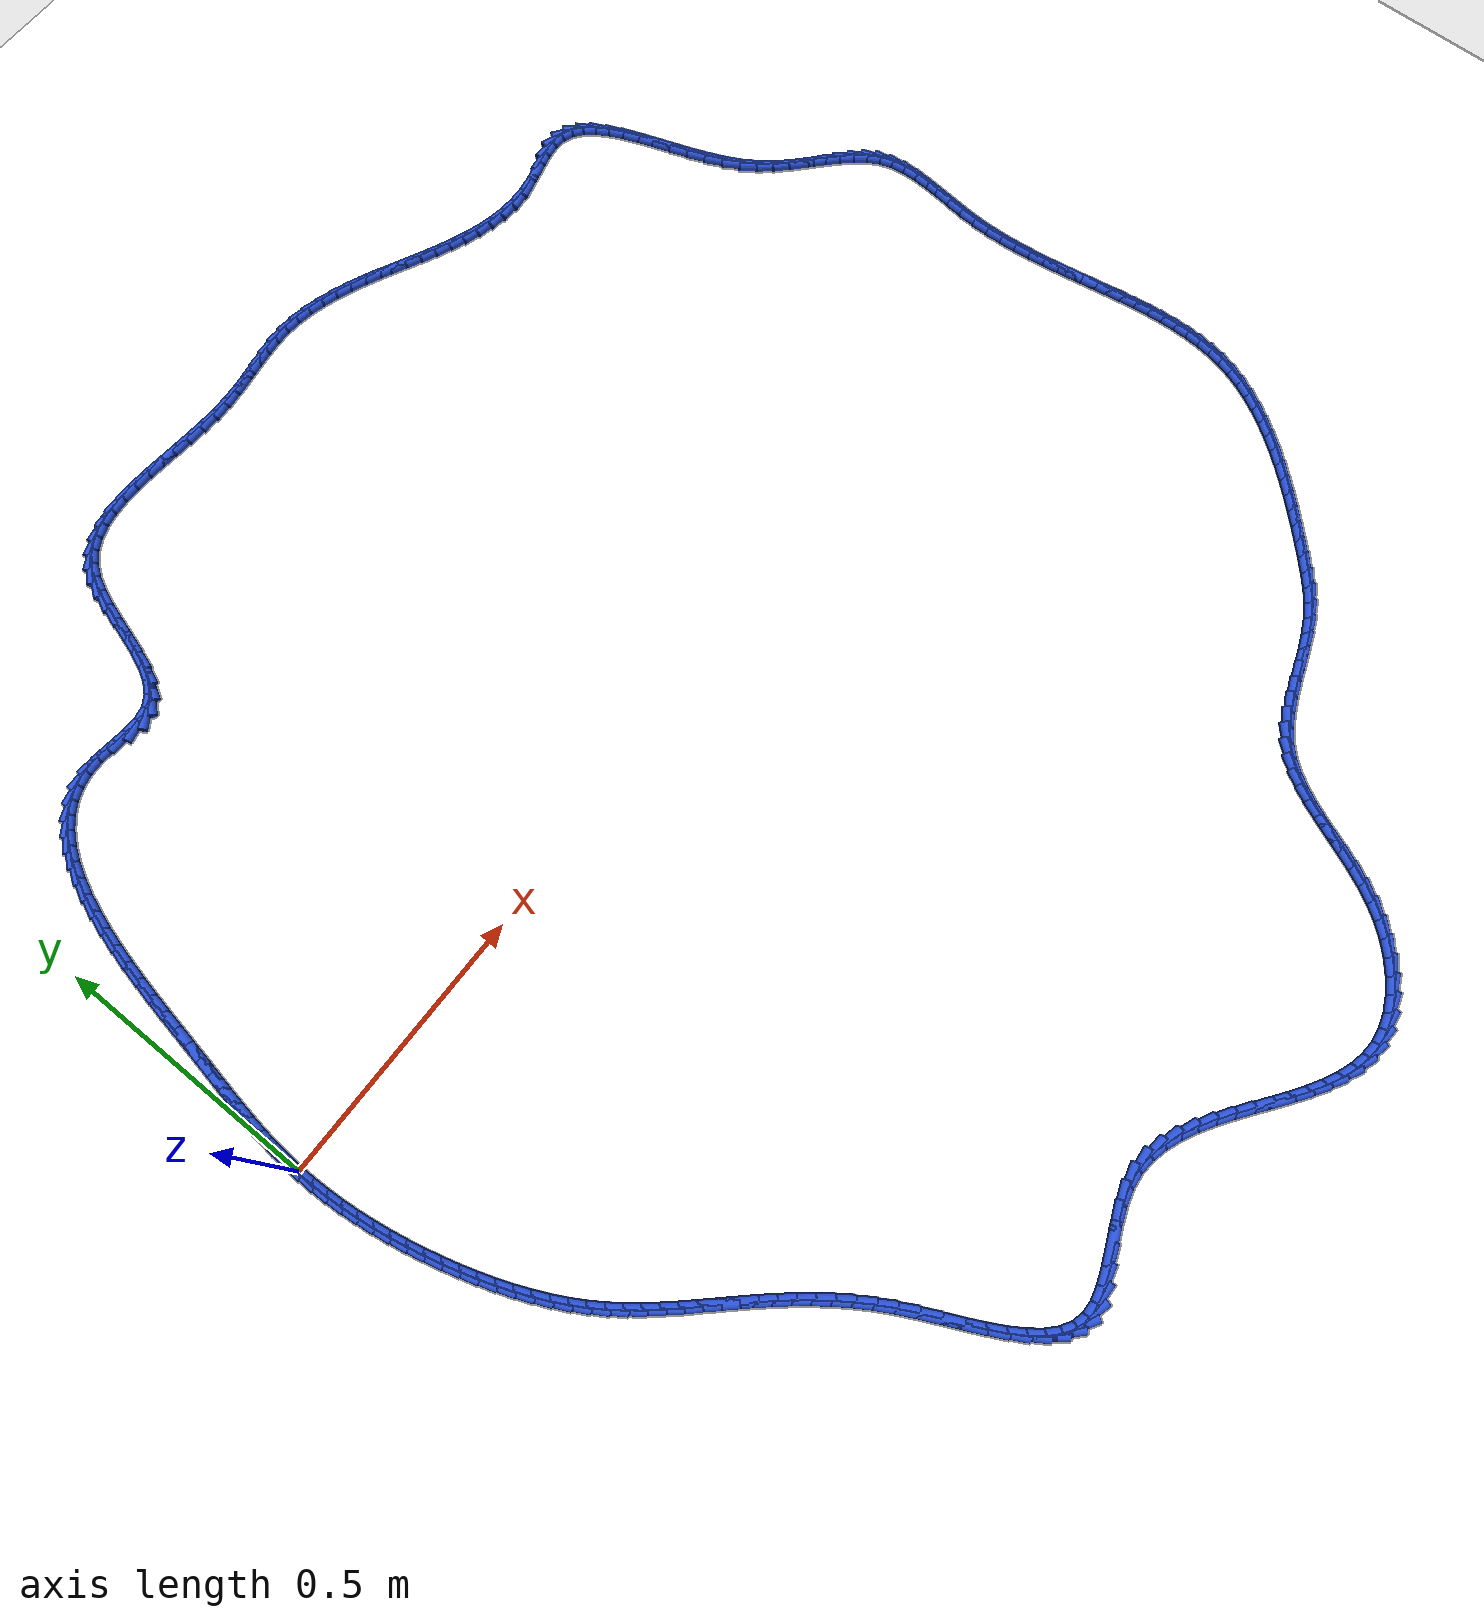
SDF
<sdf version="1.6">
 <world name="default">
  <light name="sun" type="directional">
   <pose>0 0 10 0 -0 0</pose>
   <diffuse>0.8 0.8 0.8 1</diffuse>
   <specular>0.2 0.2 0.2 1</specular>
   <attenuation>
    <range>1000</range>
    <constant>0.9</constant>
    <linear>0.01</linear>
    <quadratic>0.001</quadratic>
   </attenuation>
   <direction>-0.5 0.1 -0.9</direction>
  </light>
  <model name="ground_plane">
   <static>1</static>
   <link name="link">
    <collision name="collision">
     <geometry><plane><normal>0 0 1</normal><size>100 100</size></plane></geometry>
     <surface><friction><ode><mu>100</mu><mu2>50</mu2></ode></friction></surface>
    </collision>
    <visual name="visual">
     <cast_shadows>0</cast_shadows>
     <geometry><plane><normal>0 0 1</normal><size>100 100</size></plane></geometry>
     <material>
      <script><uri>file://media/materials/scripts/gazebo.material</uri><name>Gazebo/WhiteGlow</name></script>
     </material>
    </visual>
   </link>
  </model>
  <gravity>0 0 -9.8</gravity>
  <magnetic_field>6e-06 2.3e-05 -4.2e-05</magnetic_field>
  <atmosphere type="adiabatic"/>
  <physics name="default_physics" default="0" type="ode">
   <max_step_size>0.001</max_step_size>
   <real_time_factor>1</real_time_factor>
   <real_time_update_rate>1000</real_time_update_rate>
  </physics>
  <scene><ambient>0.4 0.4 0.4 1</ambient><background>0.7 0.7 0.7 1</background><shadows>1</shadows></scene>
  <spherical_coordinates>
   <surface_model>EARTH_WGS84</surface_model>
   <latitude_deg>0</latitude_deg>
   <longitude_deg>0</longitude_deg>
   <elevation>0</elevation>
   <heading_deg>0</heading_deg>
  </spherical_coordinates>
  <model name="line">
   <link name="link_0">
    <pose>-6.938893903907228e-18 6.938893903907228e-17 0.01 0 1.57 1.5339146569883464</pose>
    <collision name="collision">
     <geometry><cylinder><radius>0.01</radius><length>0.08</length></cylinder></geometry>
    </collision>
    <visual name="visual">
     <material>
      <script><name>Gazebo/Blue</name><uri>file://media/materials/scripts/gazebo.material</uri></script>
     </material>
     <geometry><cylinder><radius>0.01</radius><length>0.08</length></cylinder></geometry>
    </visual>
   </link>
   <link name="link_1">
    <pose>0.0010493052129371212 0.02843768734357131 0.01 0 1.57 1.4981101231882537</pose>
    <collision name="collision">
     <geometry><cylinder><radius>0.01</radius><length>0.08</length></cylinder></geometry>
    </collision>
    <visual name="visual">
     <material>
      <script><name>Gazebo/Blue</name><uri>file://media/materials/scripts/gazebo.material</uri></script>
     </material>
     <geometry><cylinder><radius>0.01</radius><length>0.08</length></cylinder></geometry>
    </visual>
   </link>
   <link name="link_2">
    <pose>0.0031059583936793324 0.0566827990900283 0.01 0 1.57 1.4670960202386527</pose>
    <collision name="collision">
     <geometry><cylinder><radius>0.01</radius><length>0.08</length></cylinder></geometry>
    </collision>
    <visual name="visual">
     <material>
      <script><name>Gazebo/Blue</name><uri>file://media/materials/scripts/gazebo.material</uri></script>
     </material>
     <geometry><cylinder><radius>0.01</radius><length>0.08</length></cylinder></geometry>
    </visual>
   </link>
   <link name="link_3">
    <pose>0.0060472240694927895 0.08494418993205767 0.01 0 1.57 1.4415249648356097</pose>
    <collision name="collision">
     <geometry><cylinder><radius>0.01</radius><length>0.08</length></cylinder></geometry>
    </collision>
    <visual name="visual">
     <material>
      <script><name>Gazebo/Blue</name><uri>file://media/materials/scripts/gazebo.material</uri></script>
     </material>
     <geometry><cylinder><radius>0.01</radius><length>0.08</length></cylinder></geometry>
    </visual>
   </link>
   <link name="link_4">
    <pose>0.009750366767643648 0.11343071456234598 0.01 0 1.57 1.4217641060363364</pose>
    <collision name="collision">
     <geometry><cylinder><radius>0.01</radius><length>0.08</length></cylinder></geometry>
    </collision>
    <visual name="visual">
     <material>
      <script><name>Gazebo/Blue</name><uri>file://media/materials/scripts/gazebo.material</uri></script>
     </material>
     <geometry><cylinder><radius>0.01</radius><length>0.08</length></cylinder></geometry>
    </visual>
   </link>
   <link name="link_5">
    <pose>0.014092651015398076 0.14235122767357986 0.01 0 1.57 1.4079041039659708</pose>
    <collision name="collision">
     <geometry><cylinder><radius>0.01</radius><length>0.08</length></cylinder></geometry>
    </collision>
    <visual name="visual">
     <material>
      <script><name>Gazebo/Blue</name><uri>file://media/materials/scripts/gazebo.material</uri></script>
     </material>
     <geometry><cylinder><radius>0.01</radius><length>0.08</length></cylinder></geometry>
    </visual>
   </link>
   <link name="link_6">
    <pose>0.01895134134002223 0.17191458395844592 0.01 0 1.57 1.3997933661096715</pose>
    <collision name="collision">
     <geometry><cylinder><radius>0.01</radius><length>0.08</length></cylinder></geometry>
    </collision>
    <visual name="visual">
     <material>
      <script><name>Gazebo/Blue</name><uri>file://media/materials/scripts/gazebo.material</uri></script>
     </material>
     <geometry><cylinder><radius>0.01</radius><length>0.08</length></cylinder></geometry>
    </visual>
   </link>
   <link name="link_7">
    <pose>0.024203702268782275 0.20232963810963076 0.01 0 1.57 1.3970862993420965</pose>
    <collision name="collision">
     <geometry><cylinder><radius>0.01</radius><length>0.08</length></cylinder></geometry>
    </collision>
    <visual name="visual">
     <material>
      <script><name>Gazebo/Blue</name><uri>file://media/materials/scripts/gazebo.material</uri></script>
     </material>
     <geometry><cylinder><radius>0.01</radius><length>0.08</length></cylinder></geometry>
    </visual>
   </link>
   <link name="link_8">
    <pose>0.029726998328944352 0.2338052448198209 0.01 0 1.57 1.3992734096021746</pose>
    <collision name="collision">
     <geometry><cylinder><radius>0.01</radius><length>0.08</length></cylinder></geometry>
    </collision>
    <visual name="visual">
     <material>
      <script><name>Gazebo/Blue</name><uri>file://media/materials/scripts/gazebo.material</uri></script>
     </material>
     <geometry><cylinder><radius>0.01</radius><length>0.08</length></cylinder></geometry>
    </visual>
   </link>
   <link name="link_9">
    <pose>0.035399047078439085 0.26654906317082605 0.01 0 1.57 1.4026593575670723</pose>
    <collision name="collision">
     <geometry><cylinder><radius>0.01</radius><length>0.08</length></cylinder></geometry>
    </collision>
    <visual name="visual">
     <material>
      <script><name>Gazebo/Blue</name><uri>file://media/materials/scripts/gazebo.material</uri></script>
     </material>
     <geometry><cylinder><radius>0.01</radius><length>0.08</length></cylinder></geometry>
    </visual>
   </link>
   <link name="link_10">
    <pose>0.04117800039227584 0.30059507546760517 0.01 0 1.57 1.400934298260555</pose>
    <collision name="collision">
     <geometry><cylinder><radius>0.01</radius><length>0.08</length></cylinder></geometry>
    </collision>
    <visual name="visual">
     <material>
      <script><name>Gazebo/Blue</name><uri>file://media/materials/scripts/gazebo.material</uri></script>
     </material>
     <geometry><cylinder><radius>0.01</radius><length>0.08</length></cylinder></geometry>
    </visual>
   </link>
   <link name="link_11">
    <pose>0.047185825791042905 0.3356231068584216 0.01 0 1.57 1.3937304232371093</pose>
    <collision name="collision">
     <geometry><cylinder><radius>0.01</radius><length>0.08</length></cylinder></geometry>
    </collision>
    <visual name="visual">
     <material>
      <script><name>Gazebo/Blue</name><uri>file://media/materials/scripts/gazebo.material</uri></script>
     </material>
     <geometry><cylinder><radius>0.01</radius><length>0.08</length></cylinder></geometry>
    </visual>
   </link>
   <link name="link_12">
    <pose>0.05356444763646478 0.3712698372956781 0.01 0 1.57 1.3811548042032664</pose>
    <collision name="collision">
     <geometry><cylinder><radius>0.01</radius><length>0.08</length></cylinder></geometry>
    </collision>
    <visual name="visual">
     <material>
      <script><name>Gazebo/Blue</name><uri>file://media/materials/scripts/gazebo.material</uri></script>
     </material>
     <geometry><cylinder><radius>0.01</radius><length>0.08</length></cylinder></geometry>
    </visual>
   </link>
   <link name="link_13">
    <pose>0.060455790290265946 0.40717194673177687 0.01 0 1.57 1.3630226083841406</pose>
    <collision name="collision">
     <geometry><cylinder><radius>0.01</radius><length>0.08</length></cylinder></geometry>
    </collision>
    <visual name="visual">
     <material>
      <script><name>Gazebo/Blue</name><uri>file://media/materials/scripts/gazebo.material</uri></script>
     </material>
     <geometry><cylinder><radius>0.01</radius><length>0.08</length></cylinder></geometry>
    </visual>
   </link>
   <link name="link_14">
    <pose>0.06800177811417094 0.4429661151191214 0.01 0 1.57 1.3388666004226362</pose>
    <collision name="collision">
     <geometry><cylinder><radius>0.01</radius><length>0.08</length></cylinder></geometry>
    </collision>
    <visual name="visual">
     <material>
      <script><name>Gazebo/Blue</name><uri>file://media/materials/scripts/gazebo.material</uri></script>
     </material>
     <geometry><cylinder><radius>0.01</radius><length>0.08</length></cylinder></geometry>
    </visual>
   </link>
   <link name="link_15">
    <pose>0.07634433546990424 0.4782890224101138 0.01 0 1.57 1.307916968639445</pose>
    <collision name="collision">
     <geometry><cylinder><radius>0.01</radius><length>0.08</length></cylinder></geometry>
    </collision>
    <visual name="visual">
     <material>
      <script><name>Gazebo/Blue</name><uri>file://media/materials/scripts/gazebo.material</uri></script>
     </material>
     <geometry><cylinder><radius>0.01</radius><length>0.08</length></cylinder></geometry>
    </visual>
   </link>
   <link name="link_16">
    <pose>0.08562538671919037 0.512777348557157 0.01 0 1.57 1.2690554530625178</pose>
    <collision name="collision">
     <geometry><cylinder><radius>0.01</radius><length>0.08</length></cylinder></geometry>
    </collision>
    <visual name="visual">
     <material>
      <script><name>Gazebo/Blue</name><uri>file://media/materials/scripts/gazebo.material</uri></script>
     </material>
     <geometry><cylinder><radius>0.01</radius><length>0.08</length></cylinder></geometry>
    </visual>
   </link>
   <link name="link_17">
    <pose>0.09598685622375386 0.5460677735126539 0.01 0 1.57 1.2207476960300736</pose>
    <collision name="collision">
     <geometry><cylinder><radius>0.01</radius><length>0.08</length></cylinder></geometry>
    </collision>
    <visual name="visual">
     <material>
      <script><name>Gazebo/Blue</name><uri>file://media/materials/scripts/gazebo.material</uri></script>
     </material>
     <geometry><cylinder><radius>0.01</radius><length>0.08</length></cylinder></geometry>
    </visual>
   </link>
   <link name="link_18">
    <pose>0.10757066834531921 0.5777969772290071 0.01 0 1.57 1.1609644568302275</pose>
    <collision name="collision">
     <geometry><cylinder><radius>0.01</radius><length>0.08</length></cylinder></geometry>
    </collision>
    <visual name="visual">
     <material>
      <script><name>Gazebo/Blue</name><uri>file://media/materials/scripts/gazebo.material</uri></script>
     </material>
     <geometry><cylinder><radius>0.01</radius><length>0.08</length></cylinder></geometry>
    </visual>
   </link>
   <link name="link_19">
    <pose>0.12051874744561092 0.6076016396586195 0.01 0 1.57 1.087122867480417</pose>
    <collision name="collision">
     <geometry><cylinder><radius>0.01</radius><length>0.08</length></cylinder></geometry>
    </collision>
    <visual name="visual">
     <material>
      <script><name>Gazebo/Blue</name><uri>file://media/materials/scripts/gazebo.material</uri></script>
     </material>
     <geometry><cylinder><radius>0.01</radius><length>0.08</length></cylinder></geometry>
    </visual>
   </link>
   <link name="link_20">
    <pose>0.1349730178863535 0.6351184407538936 0.01 0 1.57 0.9961268211682789</pose>
    <collision name="collision">
     <geometry><cylinder><radius>0.01</radius><length>0.08</length></cylinder></geometry>
    </collision>
    <visual name="visual">
     <material>
      <script><name>Gazebo/Blue</name><uri>file://media/materials/scripts/gazebo.material</uri></script>
     </material>
     <geometry><cylinder><radius>0.01</radius><length>0.08</length></cylinder></geometry>
    </visual>
   </link>
   <link name="link_21">
    <pose>0.1510754040292715 0.6599840604672322 0.01 0 1.57 0.8846766165848281</pose>
    <collision name="collision">
     <geometry><cylinder><radius>0.01</radius><length>0.08</length></cylinder></geometry>
    </collision>
    <visual name="visual">
     <material>
      <script><name>Gazebo/Blue</name><uri>file://media/materials/scripts/gazebo.material</uri></script>
     </material>
     <geometry><cylinder><radius>0.01</radius><length>0.08</length></cylinder></geometry>
    </visual>
   </link>
   <link name="link_22">
    <pose>0.16896783023608936 0.6818351787510383 0.01 0 1.57 0.7501340569856699</pose>
    <collision name="collision">
     <geometry><cylinder><radius>0.01</radius><length>0.08</length></cylinder></geometry>
    </collision>
    <visual name="visual">
     <material>
      <script><name>Gazebo/Blue</name><uri>file://media/materials/scripts/gazebo.material</uri></script>
     </material>
     <geometry><cylinder><radius>0.01</radius><length>0.08</length></cylinder></geometry>
    </visual>
   </link>
   <link name="link_23">
    <pose>0.18879222086853165 0.7003084755577142 0.01 0 1.57 0.5922050859885374</pose>
    <collision name="collision">
     <geometry><cylinder><radius>0.01</radius><length>0.08</length></cylinder></geometry>
    </collision>
    <visual name="visual">
     <material>
      <script><name>Gazebo/Blue</name><uri>file://media/materials/scripts/gazebo.material</uri></script>
     </material>
     <geometry><cylinder><radius>0.01</radius><length>0.08</length></cylinder></geometry>
    </visual>
   </link>
   <link name="link_24">
    <pose>0.21069050028832292 0.7150406308396631 0.01 0 1.57 0.41511447473688584</pose>
    <collision name="collision">
     <geometry><cylinder><radius>0.01</radius><length>0.08</length></cylinder></geometry>
    </collision>
    <visual name="visual">
     <material>
      <script><name>Gazebo/Blue</name><uri>file://media/materials/scripts/gazebo.material</uri></script>
     </material>
     <geometry><cylinder><radius>0.01</radius><length>0.08</length></cylinder></geometry>
    </visual>
   </link>
   <link name="link_25">
    <pose>0.23480459285718747 0.7256683245492871 0.01 0 1.57 0.22862825081236965</pose>
    <collision name="collision">
     <geometry><cylinder><radius>0.01</radius><length>0.08</length></cylinder></geometry>
    </collision>
    <visual name="visual">
     <material>
      <script><name>Gazebo/Blue</name><uri>file://media/materials/scripts/gazebo.material</uri></script>
     </material>
     <geometry><cylinder><radius>0.01</radius><length>0.08</length></cylinder></geometry>
    </visual>
   </link>
   <link name="link_26">
    <pose>0.26127642293685016 0.7318282366389899 0.01 0 1.57 0.04611960585594783</pose>
    <collision name="collision">
     <geometry><cylinder><radius>0.01</radius><length>0.08</length></cylinder></geometry>
    </collision>
    <visual name="visual">
     <material>
      <script><name>Gazebo/Blue</name><uri>file://media/materials/scripts/gazebo.material</uri></script>
     </material>
     <geometry><cylinder><radius>0.01</radius><length>0.08</length></cylinder></geometry>
    </visual>
   </link>
   <link name="link_27">
    <pose>0.29024352063674413 0.7331651357716622 0.01 0 1.57 -0.08573914183119526</pose>
    <collision name="collision">
     <geometry><cylinder><radius>0.01</radius><length>0.08</length></cylinder></geometry>
    </collision>
    <visual name="visual">
     <material>
      <script><name>Gazebo/Blue</name><uri>file://media/materials/scripts/gazebo.material</uri></script>
     </material>
     <geometry><cylinder><radius>0.01</radius><length>0.08</length></cylinder></geometry>
    </visual>
   </link>
   <link name="link_28">
    <pose>0.32120212363358647 0.730504248281645 0.01 0 1.57 -0.10950675645461184</pose>
    <collision name="collision">
     <geometry><cylinder><radius>0.01</radius><length>0.08</length></cylinder></geometry>
    </collision>
    <visual name="visual">
     <material>
      <script><name>Gazebo/Blue</name><uri>file://media/materials/scripts/gazebo.material</uri></script>
     </material>
     <geometry><cylinder><radius>0.01</radius><length>0.08</length></cylinder></geometry>
    </visual>
   </link>
   <link name="link_29">
    <pose>0.3523392016494445 0.7270808326854729 0.01 0 1.57 -0.022375400842900094</pose>
    <collision name="collision">
     <geometry><cylinder><radius>0.01</radius><length>0.08</length></cylinder></geometry>
    </collision>
    <visual name="visual">
     <material>
      <script><name>Gazebo/Blue</name><uri>file://media/materials/scripts/gazebo.material</uri></script>
     </material>
     <geometry><cylinder><radius>0.01</radius><length>0.08</length></cylinder></geometry>
    </visual>
   </link>
   <link name="link_30">
    <pose>0.38168199650246754 0.7264241662965774 0.01 0 1.57 0.21566609764095812</pose>
    <collision name="collision">
     <geometry><cylinder><radius>0.01</radius><length>0.08</length></cylinder></geometry>
    </collision>
    <visual name="visual">
     <material>
      <script><name>Gazebo/Blue</name><uri>file://media/materials/scripts/gazebo.material</uri></script>
     </material>
     <geometry><cylinder><radius>0.01</radius><length>0.08</length></cylinder></geometry>
    </visual>
   </link>
   <link name="link_31">
    <pose>0.4072762555149851 0.7320311819334352 0.01 0 1.57 0.5729073200740039</pose>
    <collision name="collision">
     <geometry><cylinder><radius>0.01</radius><length>0.08</length></cylinder></geometry>
    </collision>
    <visual name="visual">
     <material>
      <script><name>Gazebo/Blue</name><uri>file://media/materials/scripts/gazebo.material</uri></script>
     </material>
     <geometry><cylinder><radius>0.01</radius><length>0.08</length></cylinder></geometry>
    </visual>
   </link>
   <link name="link_32">
    <pose>0.42822755765998144 0.745546405739186 0.01 0 1.57 0.87151933151094</pose>
    <collision name="collision">
     <geometry><cylinder><radius>0.01</radius><length>0.08</length></cylinder></geometry>
    </collision>
    <visual name="visual">
     <material>
      <script><name>Gazebo/Blue</name><uri>file://media/materials/scripts/gazebo.material</uri></script>
     </material>
     <geometry><cylinder><radius>0.01</radius><length>0.08</length></cylinder></geometry>
    </visual>
   </link>
   <link name="link_33">
    <pose>0.44525582404270675 0.7657927665398421 0.01 0 1.57 1.0709350997753495</pose>
    <collision name="collision">
     <geometry><cylinder><radius>0.01</radius><length>0.08</length></cylinder></geometry>
    </collision>
    <visual name="visual">
     <material>
      <script><name>Gazebo/Blue</name><uri>file://media/materials/scripts/gazebo.material</uri></script>
     </material>
     <geometry><cylinder><radius>0.01</radius><length>0.08</length></cylinder></geometry>
    </visual>
   </link>
   <link name="link_34">
    <pose>0.45921657718199627 0.7913561847992339 0.01 0 1.57 1.191396200107836</pose>
    <collision name="collision">
     <geometry><cylinder><radius>0.01</radius><length>0.08</length></cylinder></geometry>
    </collision>
    <visual name="visual">
     <material>
      <script><name>Gazebo/Blue</name><uri>file://media/materials/scripts/gazebo.material</uri></script>
     </material>
     <geometry><cylinder><radius>0.01</radius><length>0.08</length></cylinder></geometry>
    </visual>
   </link>
   <link name="link_35">
    <pose>0.47096533959668585 0.8208225809811924 0.01 0 1.57 1.2563713075496996</pose>
    <collision name="collision">
     <geometry><cylinder><radius>0.01</radius><length>0.08</length></cylinder></geometry>
    </collision>
    <visual name="visual">
     <material>
      <script><name>Gazebo/Blue</name><uri>file://media/materials/scripts/gazebo.material</uri></script>
     </material>
     <geometry><cylinder><radius>0.01</radius><length>0.08</length></cylinder></geometry>
    </visual>
   </link>
   <link name="link_36">
    <pose>0.4813576338056106 0.852777875549548 0.01 0 1.57 1.2798308301384231</pose>
    <collision name="collision">
     <geometry><cylinder><radius>0.01</radius><length>0.08</length></cylinder></geometry>
    </collision>
    <visual name="visual">
     <material>
      <script><name>Gazebo/Blue</name><uri>file://media/materials/scripts/gazebo.material</uri></script>
     </material>
     <geometry><cylinder><radius>0.01</radius><length>0.08</length></cylinder></geometry>
    </visual>
   </link>
   <link name="link_37">
    <pose>0.4912489823276059 0.8858079889681314 0.01 0 1.57 1.2670746903792205</pose>
    <collision name="collision">
     <geometry><cylinder><radius>0.01</radius><length>0.08</length></cylinder></geometry>
    </collision>
    <visual name="visual">
     <material>
      <script><name>Gazebo/Blue</name><uri>file://media/materials/scripts/gazebo.material</uri></script>
     </material>
     <geometry><cylinder><radius>0.01</radius><length>0.08</length></cylinder></geometry>
    </visual>
   </link>
   <link name="link_38">
    <pose>0.5014949076815073 0.918498841700773 0.01 0 1.57 1.2161564289155946</pose>
    <collision name="collision">
     <geometry><cylinder><radius>0.01</radius><length>0.08</length></cylinder></geometry>
    </collision>
    <visual name="visual">
     <material>
      <script><name>Gazebo/Blue</name><uri>file://media/materials/scripts/gazebo.material</uri></script>
     </material>
     <geometry><cylinder><radius>0.01</radius><length>0.08</length></cylinder></geometry>
    </visual>
   </link>
   <link name="link_39">
    <pose>0.51295093238615 0.9494363542113032 0.01 0 1.57 1.1176722262518997</pose>
    <collision name="collision">
     <geometry><cylinder><radius>0.01</radius><length>0.08</length></cylinder></geometry>
    </collision>
    <visual name="visual">
     <material>
      <script><name>Gazebo/Blue</name><uri>file://media/materials/scripts/gazebo.material</uri></script>
     </material>
     <geometry><cylinder><radius>0.01</radius><length>0.08</length></cylinder></geometry>
    </visual>
   </link>
   <link name="link_40">
    <pose>0.5264725789603693 0.977206446963553 0.01 0 1.57 0.9545355267099519</pose>
    <collision name="collision">
     <geometry><cylinder><radius>0.01</radius><length>0.08</length></cylinder></geometry>
    </collision>
    <visual name="visual">
     <material>
      <script><name>Gazebo/Blue</name><uri>file://media/materials/scripts/gazebo.material</uri></script>
     </material>
     <geometry><cylinder><radius>0.01</radius><length>0.08</length></cylinder></geometry>
    </visual>
   </link>
   <link name="link_41">
    <pose>0.5429067270728724 1.0004093748785523 0.01 0 1.57 0.7395651632823327</pose>
    <collision name="collision">
     <geometry><cylinder><radius>0.01</radius><length>0.08</length></cylinder></geometry>
    </collision>
    <visual name="visual">
     <material>
      <script><name>Gazebo/Blue</name><uri>file://media/materials/scripts/gazebo.material</uri></script>
     </material>
     <geometry><cylinder><radius>0.01</radius><length>0.08</length></cylinder></geometry>
    </visual>
   </link>
   <link name="link_42">
    <pose>0.5626387755978016 1.018410774273498 0.01 0 1.57 0.5294057698637827</pose>
    <collision name="collision">
     <geometry><cylinder><radius>0.01</radius><length>0.08</length></cylinder></geometry>
    </collision>
    <visual name="visual">
     <material>
      <script><name>Gazebo/Blue</name><uri>file://media/materials/scripts/gazebo.material</uri></script>
     </material>
     <geometry><cylinder><radius>0.01</radius><length>0.08</length></cylinder></geometry>
    </visual>
   </link>
   <link name="link_43">
    <pose>0.585369855658512 1.0317111625107334 0.01 0 1.57 0.3475228646965846</pose>
    <collision name="collision">
     <geometry><cylinder><radius>0.01</radius><length>0.08</length></cylinder></geometry>
    </collision>
    <visual name="visual">
     <material>
      <script><name>Gazebo/Blue</name><uri>file://media/materials/scripts/gazebo.material</uri></script>
     </material>
     <geometry><cylinder><radius>0.01</radius><length>0.08</length></cylinder></geometry>
    </visual>
   </link>
   <link name="link_44">
    <pose>0.61074571939367 1.0409029048585532 0.01 0 1.57 0.2023321326701592</pose>
    <collision name="collision">
     <geometry><cylinder><radius>0.01</radius><length>0.08</length></cylinder></geometry>
    </collision>
    <visual name="visual">
     <material>
      <script><name>Gazebo/Blue</name><uri>file://media/materials/scripts/gazebo.material</uri></script>
     </material>
     <geometry><cylinder><radius>0.01</radius><length>0.08</length></cylinder></geometry>
    </visual>
   </link>
   <link name="link_45">
    <pose>0.6384121189419433 1.0465783665852537 0.01 0 1.57 0.09268290767409672</pose>
    <collision name="collision">
     <geometry><cylinder><radius>0.01</radius><length>0.08</length></cylinder></geometry>
    </collision>
    <visual name="visual">
     <material>
      <script><name>Gazebo/Blue</name><uri>file://media/materials/scripts/gazebo.material</uri></script>
     </material>
     <geometry><cylinder><radius>0.01</radius><length>0.08</length></cylinder></geometry>
    </visual>
   </link>
   <link name="link_46">
    <pose>0.6680148064419984 1.0493299129591303 0.01 0 1.57 0.013467197906035195</pose>
    <collision name="collision">
     <geometry><cylinder><radius>0.01</radius><length>0.08</length></cylinder></geometry>
    </collision>
    <visual name="visual">
     <material>
      <script><name>Gazebo/Blue</name><uri>file://media/materials/scripts/gazebo.material</uri></script>
     </material>
     <geometry><cylinder><radius>0.01</radius><length>0.08</length></cylinder></geometry>
    </visual>
   </link>
   <link name="link_47">
    <pose>0.699199534032503 1.0497499092484788 0.01 0 1.57 -0.04067751754340314</pose>
    <collision name="collision">
     <geometry><cylinder><radius>0.01</radius><length>0.08</length></cylinder></geometry>
    </collision>
    <visual name="visual">
     <material>
      <script><name>Gazebo/Blue</name><uri>file://media/materials/scripts/gazebo.material</uri></script>
     </material>
     <geometry><cylinder><radius>0.01</radius><length>0.08</length></cylinder></geometry>
    </visual>
   </link>
   <link name="link_48">
    <pose>0.7316120538521242 1.0484307207215953 0.01 0 1.57 -0.07395020302191643</pose>
    <collision name="collision">
     <geometry><cylinder><radius>0.01</radius><length>0.08</length></cylinder></geometry>
    </collision>
    <visual name="visual">
     <material>
      <script><name>Gazebo/Blue</name><uri>file://media/materials/scripts/gazebo.material</uri></script>
     </material>
     <geometry><cylinder><radius>0.01</radius><length>0.08</length></cylinder></geometry>
    </visual>
   </link>
   <link name="link_49">
    <pose>0.7648981180395286 1.0459647126467746 0.01 0 1.57 -0.08911199130429608</pose>
    <collision name="collision">
     <geometry><cylinder><radius>0.01</radius><length>0.08</length></cylinder></geometry>
    </collision>
    <visual name="visual">
     <material>
      <script><name>Gazebo/Blue</name><uri>file://media/materials/scripts/gazebo.material</uri></script>
     </material>
     <geometry><cylinder><radius>0.01</radius><length>0.08</length></cylinder></geometry>
    </visual>
   </link>
   <link name="link_50">
    <pose>0.7987034787333841 1.0429442502923134 0.01 0 1.57 -0.08757394837977431</pose>
    <collision name="collision">
     <geometry><cylinder><radius>0.01</radius><length>0.08</length></cylinder></geometry>
    </collision>
    <visual name="visual">
     <material>
      <script><name>Gazebo/Blue</name><uri>file://media/materials/scripts/gazebo.material</uri></script>
     </material>
     <geometry><cylinder><radius>0.01</radius><length>0.08</length></cylinder></geometry>
    </visual>
   </link>
   <link name="link_51">
    <pose>0.8326738880723573 1.0399616989265068 0.01 0 1.57 -0.0695204314073739</pose>
    <collision name="collision">
     <geometry><cylinder><radius>0.01</radius><length>0.08</length></cylinder></geometry>
    </collision>
    <visual name="visual">
     <material>
      <script><name>Gazebo/Blue</name><uri>file://media/materials/scripts/gazebo.material</uri></script>
     </material>
     <geometry><cylinder><radius>0.01</radius><length>0.08</length></cylinder></geometry>
    </visual>
   </link>
   <link name="link_52">
    <pose>0.8664550981951156 1.0376094238176508 0.01 0 1.57 -0.03397337373920289</pose>
    <collision name="collision">
     <geometry><cylinder><radius>0.01</radius><length>0.08</length></cylinder></geometry>
    </collision>
    <visual name="visual">
     <material>
      <script><name>Gazebo/Blue</name><uri>file://media/materials/scripts/gazebo.material</uri></script>
     </material>
     <geometry><cylinder><radius>0.01</radius><length>0.08</length></cylinder></geometry>
    </visual>
   </link>
   <link name="link_53">
    <pose>0.8996928612403259 1.036479790234041 0.01 0 1.57 0.02117701443042391</pose>
    <collision name="collision">
     <geometry><cylinder><radius>0.01</radius><length>0.08</length></cylinder></geometry>
    </collision>
    <visual name="visual">
     <material>
      <script><name>Gazebo/Blue</name><uri>file://media/materials/scripts/gazebo.material</uri></script>
     </material>
     <geometry><cylinder><radius>0.01</radius><length>0.08</length></cylinder></geometry>
    </visual>
   </link>
   <link name="link_54">
    <pose>0.93203308807381 1.0371647620829532 0.01 0 1.57 0.08793731890708004</pose>
    <collision name="collision">
     <geometry><cylinder><radius>0.01</radius><length>0.08</length></cylinder></geometry>
    </collision>
    <visual name="visual">
     <material>
      <script><name>Gazebo/Blue</name><uri>file://media/materials/scripts/gazebo.material</uri></script>
     </material>
     <geometry><cylinder><radius>0.01</radius><length>0.08</length></cylinder></geometry>
    </visual>
   </link>
   <link name="link_55">
    <pose>0.9632556798854693 1.039917492352317 0.01 0 1.57 0.1352688795808788</pose>
    <collision name="collision">
     <geometry><cylinder><radius>0.01</radius><length>0.08</length></cylinder></geometry>
    </collision>
    <visual name="visual">
     <material>
      <script><name>Gazebo/Blue</name><uri>file://media/materials/scripts/gazebo.material</uri></script>
     </material>
     <geometry><cylinder><radius>0.01</radius><length>0.08</length></cylinder></geometry>
    </visual>
   </link>
   <link name="link_56">
    <pose>0.9935181804309821 1.0440362186227528 0.01 0 1.57 0.15507944825660466</pose>
    <collision name="collision">
     <geometry><cylinder><radius>0.01</radius><length>0.08</length></cylinder></geometry>
    </collision>
    <visual name="visual">
     <material>
      <script><name>Gazebo/Blue</name><uri>file://media/materials/scripts/gazebo.material</uri></script>
     </material>
     <geometry><cylinder><radius>0.01</radius><length>0.08</length></cylinder></geometry>
    </visual>
   </link>
   <link name="link_57">
    <pose>1.0230441852304586 1.0486521585114175 0.01 0 1.57 0.14526111254245366</pose>
    <collision name="collision">
     <geometry><cylinder><radius>0.01</radius><length>0.08</length></cylinder></geometry>
    </collision>
    <visual name="visual">
     <material>
      <script><name>Gazebo/Blue</name><uri>file://media/materials/scripts/gazebo.material</uri></script>
     </material>
     <geometry><cylinder><radius>0.01</radius><length>0.08</length></cylinder></geometry>
    </visual>
   </link>
   <link name="link_58">
    <pose>1.0520572898040104 1.0528965296354693 0.01 0 1.57 0.1042041462762869</pose>
    <collision name="collision">
     <geometry><cylinder><radius>0.01</radius><length>0.08</length></cylinder></geometry>
    </collision>
    <visual name="visual">
     <material>
      <script><name>Gazebo/Blue</name><uri>file://media/materials/scripts/gazebo.material</uri></script>
     </material>
     <geometry><cylinder><radius>0.01</radius><length>0.08</length></cylinder></geometry>
    </visual>
   </link>
   <link name="link_59">
    <pose>1.0807810896717482 1.0559005496120655 0.01 0 1.57 0.03121616731461939</pose>
    <collision name="collision">
     <geometry><cylinder><radius>0.01</radius><length>0.08</length></cylinder></geometry>
    </collision>
    <visual name="visual">
     <material>
      <script><name>Gazebo/Blue</name><uri>file://media/materials/scripts/gazebo.material</uri></script>
     </material>
     <geometry><cylinder><radius>0.01</radius><length>0.08</length></cylinder></geometry>
    </visual>
   </link>
   <link name="link_60">
    <pose>1.1094391803537835 1.056795436058363 0.01 0 1.57 -0.06659063743221426</pose>
    <collision name="collision">
     <geometry><cylinder><radius>0.01</radius><length>0.08</length></cylinder></geometry>
    </collision>
    <visual name="visual">
     <material>
      <script><name>Gazebo/Blue</name><uri>file://media/materials/scripts/gazebo.material</uri></script>
     </material>
     <geometry><cylinder><radius>0.01</radius><length>0.08</length></cylinder></geometry>
    </visual>
   </link>
   <link name="link_61">
    <pose>1.1382141633560712 1.0548764543040272 0.01 0 1.57 -0.15920112076810233</pose>
    <collision name="collision">
     <geometry><cylinder><radius>0.01</radius><length>0.08</length></cylinder></geometry>
    </collision>
    <visual name="visual">
     <material>
      <script><name>Gazebo/Blue</name><uri>file://media/materials/scripts/gazebo.material</uri></script>
     </material>
     <geometry><cylinder><radius>0.01</radius><length>0.08</length></cylinder></geometry>
    </visual>
   </link>
   <link name="link_62">
    <pose>1.1670883401589136 1.050240419897703 0.01 0 1.57 -0.23806759459187515</pose>
    <collision name="collision">
     <geometry><cylinder><radius>0.01</radius><length>0.08</length></cylinder></geometry>
    </collision>
    <visual name="visual">
     <material>
      <script><name>Gazebo/Blue</name><uri>file://media/materials/scripts/gazebo.material</uri></script>
     </material>
     <geometry><cylinder><radius>0.01</radius><length>0.08</length></cylinder></geometry>
    </visual>
   </link>
   <link name="link_63">
    <pose>1.1959829302676999 1.0432285830565193 0.01 0 1.57 -0.303990715160315</pose>
    <collision name="collision">
     <geometry><cylinder><radius>0.01</radius><length>0.08</length></cylinder></geometry>
    </collision>
    <visual name="visual">
     <material>
      <script><name>Gazebo/Blue</name><uri>file://media/materials/scripts/gazebo.material</uri></script>
     </material>
     <geometry><cylinder><radius>0.01</radius><length>0.08</length></cylinder></geometry>
    </visual>
   </link>
   <link name="link_64">
    <pose>1.2248191383475184 1.034182253384738 0.01 0 1.57 -0.35807937355999697</pose>
    <collision name="collision">
     <geometry><cylinder><radius>0.01</radius><length>0.08</length></cylinder></geometry>
    </collision>
    <visual name="visual">
     <material>
      <script><name>Gazebo/Blue</name><uri>file://media/materials/scripts/gazebo.material</uri></script>
     </material>
     <geometry><cylinder><radius>0.01</radius><length>0.08</length></cylinder></geometry>
    </visual>
   </link>
   <link name="link_65">
    <pose>1.2535181690634607 1.0234427404866215 0.01 0 1.57 -0.40145683568590046</pose>
    <collision name="collision">
     <geometry><cylinder><radius>0.01</radius><length>0.08</length></cylinder></geometry>
    </collision>
    <visual name="visual">
     <material>
      <script><name>Gazebo/Blue</name><uri>file://media/materials/scripts/gazebo.material</uri></script>
     </material>
     <geometry><cylinder><radius>0.01</radius><length>0.08</length></cylinder></geometry>
    </visual>
   </link>
   <link name="link_66">
    <pose>1.2820012270806178 1.0113513539664323 0.01 0 1.57 -0.4346371529740864</pose>
    <collision name="collision">
     <geometry><cylinder><radius>0.01</radius><length>0.08</length></cylinder></geometry>
    </collision>
    <visual name="visual">
     <material>
      <script><name>Gazebo/Blue</name><uri>file://media/materials/scripts/gazebo.material</uri></script>
     </material>
     <geometry><cylinder><radius>0.01</radius><length>0.08</length></cylinder></geometry>
    </visual>
   </link>
   <link name="link_67">
    <pose>1.310209523903029 0.998255778376063 0.01 0 1.57 -0.45589552437854947</pose>
    <collision name="collision">
     <geometry><cylinder><radius>0.01</radius><length>0.08</length></cylinder></geometry>
    </collision>
    <visual name="visual">
     <material>
      <script><name>Gazebo/Blue</name><uri>file://media/materials/scripts/gazebo.material</uri></script>
     </material>
     <geometry><cylinder><radius>0.01</radius><length>0.08</length></cylinder></geometry>
    </visual>
   </link>
   <link name="link_68">
    <pose>1.3381878306703134 0.9845366963464692 0.01 0 1.57 -0.4647398906761913</pose>
    <collision name="collision">
     <geometry><cylinder><radius>0.01</radius><length>0.08</length></cylinder></geometry>
    </collision>
    <visual name="visual">
     <material>
      <script><name>Gazebo/Blue</name><uri>file://media/materials/scripts/gazebo.material</uri></script>
     </material>
     <geometry><cylinder><radius>0.01</radius><length>0.08</length></cylinder></geometry>
    </visual>
   </link>
   <link name="link_69">
    <pose>1.366014325423496 0.9705854352310186 0.01 0 1.57 -0.46121374476185983</pose>
    <collision name="collision">
     <geometry><cylinder><radius>0.01</radius><length>0.08</length></cylinder></geometry>
    </collision>
    <visual name="visual">
     <material>
      <script><name>Gazebo/Blue</name><uri>file://media/materials/scripts/gazebo.material</uri></script>
     </material>
     <geometry><cylinder><radius>0.01</radius><length>0.08</length></cylinder></geometry>
    </visual>
   </link>
   <link name="link_70">
    <pose>1.3937672025947738 0.9567933276059359 0.01 0 1.57 -0.4451175134729485</pose>
    <collision name="collision">
     <geometry><cylinder><radius>0.01</radius><length>0.08</length></cylinder></geometry>
    </collision>
    <visual name="visual">
     <material>
      <script><name>Gazebo/Blue</name><uri>file://media/materials/scripts/gazebo.material</uri></script>
     </material>
     <geometry><cylinder><radius>0.01</radius><length>0.08</length></cylinder></geometry>
    </visual>
   </link>
   <link name="link_71">
    <pose>1.4215246566163435 0.9435517060474471 0.01 0 1.57 -0.416013657188687</pose>
    <collision name="collision">
     <geometry><cylinder><radius>0.01</radius><length>0.08</length></cylinder></geometry>
    </collision>
    <visual name="visual">
     <material>
      <script><name>Gazebo/Blue</name><uri>file://media/materials/scripts/gazebo.material</uri></script>
     </material>
     <geometry><cylinder><radius>0.01</radius><length>0.08</length></cylinder></geometry>
    </visual>
   </link>
   <link name="link_72">
    <pose>1.449364881920404 0.9312519031317767 0.01 0 1.57 -0.3732869835336579</pose>
    <collision name="collision">
     <geometry><cylinder><radius>0.01</radius><length>0.08</length></cylinder></geometry>
    </collision>
    <visual name="visual">
     <material>
      <script><name>Gazebo/Blue</name><uri>file://media/materials/scripts/gazebo.material</uri></script>
     </material>
     <geometry><cylinder><radius>0.01</radius><length>0.08</length></cylinder></geometry>
    </visual>
   </link>
   <link name="link_73">
    <pose>1.4773660729391522 0.9202852514351507 0.01 0 1.57 -0.31628200689793046</pose>
    <collision name="collision">
     <geometry><cylinder><radius>0.01</radius><length>0.08</length></cylinder></geometry>
    </collision>
    <visual name="visual">
     <material>
      <script><name>Gazebo/Blue</name><uri>file://media/materials/scripts/gazebo.material</uri></script>
     </material>
     <geometry><cylinder><radius>0.01</radius><length>0.08</length></cylinder></geometry>
    </visual>
   </link>
   <link name="link_74">
    <pose>1.5056064241047866 0.9110430835337937 0.01 0 1.57 -0.24454770696590786</pose>
    <collision name="collision">
     <geometry><cylinder><radius>0.01</radius><length>0.08</length></cylinder></geometry>
    </collision>
    <visual name="visual">
     <material>
      <script><name>Gazebo/Blue</name><uri>file://media/materials/scripts/gazebo.material</uri></script>
     </material>
     <geometry><cylinder><radius>0.01</radius><length>0.08</length></cylinder></geometry>
    </visual>
   </link>
   <link name="link_75">
    <pose>1.534164129849504 0.9039167320039315 0.01 0 1.57 -0.15820672280961398</pose>
    <collision name="collision">
     <geometry><cylinder><radius>0.01</radius><length>0.08</length></cylinder></geometry>
    </collision>
    <visual name="visual">
     <material>
      <script><name>Gazebo/Blue</name><uri>file://media/materials/scripts/gazebo.material</uri></script>
     </material>
     <geometry><cylinder><radius>0.01</radius><length>0.08</length></cylinder></geometry>
    </visual>
   </link>
   <link name="link_76">
    <pose>1.5631173846055015 0.8992975294217889 0.01 0 1.57 -0.05840772057856388</pose>
    <collision name="collision">
     <geometry><cylinder><radius>0.01</radius><length>0.08</length></cylinder></geometry>
    </collision>
    <visual name="visual">
     <material>
      <script><name>Gazebo/Blue</name><uri>file://media/materials/scripts/gazebo.material</uri></script>
     </material>
     <geometry><cylinder><radius>0.01</radius><length>0.08</length></cylinder></geometry>
    </visual>
   </link>
   <link name="link_77">
    <pose>1.5925443828049772 0.8975768083635911 0.01 0 1.57 0.052292134917893925</pose>
    <collision name="collision">
     <geometry><cylinder><radius>0.01</radius><length>0.08</length></cylinder></geometry>
    </collision>
    <visual name="visual">
     <material>
      <script><name>Gazebo/Blue</name><uri>file://media/materials/scripts/gazebo.material</uri></script>
     </material>
     <geometry><cylinder><radius>0.01</radius><length>0.08</length></cylinder></geometry>
    </visual>
   </link>
   <link name="link_78">
    <pose>1.62252331888013 0.8991459014055637 0.01 0 1.57 0.16843909581495528</pose>
    <collision name="collision">
     <geometry><cylinder><radius>0.01</radius><length>0.08</length></cylinder></geometry>
    </collision>
    <visual name="visual">
     <material>
      <script><name>Gazebo/Blue</name><uri>file://media/materials/scripts/gazebo.material</uri></script>
     </material>
     <geometry><cylinder><radius>0.01</radius><length>0.08</length></cylinder></geometry>
    </visual>
   </link>
   <link name="link_79">
    <pose>1.6531147956445158 0.9043479928407998 0.01 0 1.57 0.246419456238911</pose>
    <collision name="collision">
     <geometry><cylinder><radius>0.01</radius><length>0.08</length></cylinder></geometry>
    </collision>
    <visual name="visual">
     <material>
      <script><name>Gazebo/Blue</name><uri>file://media/materials/scripts/gazebo.material</uri></script>
     </material>
     <geometry><cylinder><radius>0.01</radius><length>0.08</length></cylinder></geometry>
    </visual>
   </link>
   <link name="link_80">
    <pose>1.6838506464597114 0.9120790242835288 0.01 0 1.57 0.24621888849881454</pose>
    <collision name="collision">
     <geometry><cylinder><radius>0.01</radius><length>0.08</length></cylinder></geometry>
    </collision>
    <visual name="visual">
     <material>
      <script><name>Gazebo/Blue</name><uri>file://media/materials/scripts/gazebo.material</uri></script>
     </material>
     <geometry><cylinder><radius>0.01</radius><length>0.08</length></cylinder></geometry>
    </visual>
   </link>
   <link name="link_81">
    <pose>1.7136540949832957 0.9195691717953438 0.01 0 1.57 0.1567446117254684</pose>
    <collision name="collision">
     <geometry><cylinder><radius>0.01</radius><length>0.08</length></cylinder></geometry>
    </collision>
    <visual name="visual">
     <material>
      <script><name>Gazebo/Blue</name><uri>file://media/materials/scripts/gazebo.material</uri></script>
     </material>
     <geometry><cylinder><radius>0.01</radius><length>0.08</length></cylinder></geometry>
    </visual>
   </link>
   <link name="link_82">
    <pose>1.7414147061505718 0.923956487471135 0.01 0 1.57 -0.058823728341692555</pose>
    <collision name="collision">
     <geometry><cylinder><radius>0.01</radius><length>0.08</length></cylinder></geometry>
    </collision>
    <visual name="visual">
     <material>
      <script><name>Gazebo/Blue</name><uri>file://media/materials/scripts/gazebo.material</uri></script>
     </material>
     <geometry><cylinder><radius>0.01</radius><length>0.08</length></cylinder></geometry>
    </visual>
   </link>
   <link name="link_83">
    <pose>1.76607659959248 0.9225041073741331 0.01 0 1.57 -0.36235637092920775</pose>
    <collision name="collision">
     <geometry><cylinder><radius>0.01</radius><length>0.08</length></cylinder></geometry>
    </collision>
    <visual name="visual">
     <material>
      <script><name>Gazebo/Blue</name><uri>file://media/materials/scripts/gazebo.material</uri></script>
     </material>
     <geometry><cylinder><radius>0.01</radius><length>0.08</length></cylinder></geometry>
    </visual>
   </link>
   <link name="link_84">
    <pose>1.787427753654674 0.9144099817119741 0.01 0 1.57 -0.6485422178990449</pose>
    <collision name="collision">
     <geometry><cylinder><radius>0.01</radius><length>0.08</length></cylinder></geometry>
    </collision>
    <visual name="visual">
     <material>
      <script><name>Gazebo/Blue</name><uri>file://media/materials/scripts/gazebo.material</uri></script>
     </material>
     <geometry><cylinder><radius>0.01</radius><length>0.08</length></cylinder></geometry>
    </visual>
   </link>
   <link name="link_85">
    <pose>1.805920140667035 0.9003944778103256 0.01 0 1.57 -0.8722530127503931</pose>
    <collision name="collision">
     <geometry><cylinder><radius>0.01</radius><length>0.08</length></cylinder></geometry>
    </collision>
    <visual name="visual">
     <material>
      <script><name>Gazebo/Blue</name><uri>file://media/materials/scripts/gazebo.material</uri></script>
     </material>
     <geometry><cylinder><radius>0.01</radius><length>0.08</length></cylinder></geometry>
    </visual>
   </link>
   <link name="link_86">
    <pose>1.8220236654863038 0.8812190790087221 0.01 0 1.57 -1.0291213548574096</pose>
    <collision name="collision">
     <geometry><cylinder><radius>0.01</radius><length>0.08</length></cylinder></geometry>
    </collision>
    <visual name="visual">
     <material>
      <script><name>Gazebo/Blue</name><uri>file://media/materials/scripts/gazebo.material</uri></script>
     </material>
     <geometry><cylinder><radius>0.01</radius><length>0.08</length></cylinder></geometry>
    </visual>
   </link>
   <link name="link_87">
    <pose>1.8362082329692222 0.8576452686466974 0.01 0 1.57 -1.133048025057399</pose>
    <collision name="collision">
     <geometry><cylinder><radius>0.01</radius><length>0.08</length></cylinder></geometry>
    </collision>
    <visual name="visual">
     <material>
      <script><name>Gazebo/Blue</name><uri>file://media/materials/scripts/gazebo.material</uri></script>
     </material>
     <geometry><cylinder><radius>0.01</radius><length>0.08</length></cylinder></geometry>
    </visual>
   </link>
   <link name="link_88">
    <pose>1.8489437479725324 0.8304345300637854 0.01 0 1.57 -1.1982839200838664</pose>
    <collision name="collision">
     <geometry><cylinder><radius>0.01</radius><length>0.08</length></cylinder></geometry>
    </collision>
    <visual name="visual">
     <material>
      <script><name>Gazebo/Blue</name><uri>file://media/materials/scripts/gazebo.material</uri></script>
     </material>
     <geometry><cylinder><radius>0.01</radius><length>0.08</length></cylinder></geometry>
    </visual>
   </link>
   <link name="link_89">
    <pose>1.860700115352976 0.8003483465995199 0.01 0 1.57 -1.2347559364976086</pose>
    <collision name="collision">
     <geometry><cylinder><radius>0.01</radius><length>0.08</length></cylinder></geometry>
    </collision>
    <visual name="visual">
     <material>
      <script><name>Gazebo/Blue</name><uri>file://media/materials/scripts/gazebo.material</uri></script>
     </material>
     <geometry><cylinder><radius>0.01</radius><length>0.08</length></cylinder></geometry>
    </visual>
   </link>
   <link name="link_90">
    <pose>1.871947239967294 0.7681482015934351 0.01 0 1.57 -1.24841343447321</pose>
    <collision name="collision">
     <geometry><cylinder><radius>0.01</radius><length>0.08</length></cylinder></geometry>
    </collision>
    <visual name="visual">
     <material>
      <script><name>Gazebo/Blue</name><uri>file://media/materials/scripts/gazebo.material</uri></script>
     </material>
     <geometry><cylinder><radius>0.01</radius><length>0.08</length></cylinder></geometry>
    </visual>
   </link>
   <link name="link_91">
    <pose>1.8831550266722292 0.7345955783850652 0.01 0 1.57 -1.242282938332239</pose>
    <collision name="collision">
     <geometry><cylinder><radius>0.01</radius><length>0.08</length></cylinder></geometry>
    </collision>
    <visual name="visual">
     <material>
      <script><name>Gazebo/Blue</name><uri>file://media/materials/scripts/gazebo.material</uri></script>
     </material>
     <geometry><cylinder><radius>0.01</radius><length>0.08</length></cylinder></geometry>
    </visual>
   </link>
   <link name="link_92">
    <pose>1.8947933803245223 0.7004519603139437 0.01 0 1.57 -1.2172252776160262</pose>
    <collision name="collision">
     <geometry><cylinder><radius>0.01</radius><length>0.08</length></cylinder></geometry>
    </collision>
    <visual name="visual">
     <material>
      <script><name>Gazebo/Blue</name><uri>file://media/materials/scripts/gazebo.material</uri></script>
     </material>
     <geometry><cylinder><radius>0.01</radius><length>0.08</length></cylinder></geometry>
    </visual>
   </link>
   <link name="link_93">
    <pose>1.9073322057809154 0.6664788307196042 0.01 0 1.57 -1.1723475183427303</pose>
    <collision name="collision">
     <geometry><cylinder><radius>0.01</radius><length>0.08</length></cylinder></geometry>
    </collision>
    <visual name="visual">
     <material>
      <script><name>Gazebo/Blue</name><uri>file://media/materials/scripts/gazebo.material</uri></script>
     </material>
     <geometry><cylinder><radius>0.01</radius><length>0.08</length></cylinder></geometry>
    </visual>
   </link>
   <link name="link_94">
    <pose>1.921241407898149 0.6334376729415814 0.01 0 1.57 -1.1052204282376692</pose>
    <collision name="collision">
     <geometry><cylinder><radius>0.01</radius><length>0.08</length></cylinder></geometry>
    </collision>
    <visual name="visual">
     <material>
      <script><name>Gazebo/Blue</name><uri>file://media/materials/scripts/gazebo.material</uri></script>
     </material>
     <geometry><cylinder><radius>0.01</radius><length>0.08</length></cylinder></geometry>
    </visual>
   </link>
   <link name="link_95">
    <pose>1.9369908915329666 0.6020899703194091 0.01 0 1.57 -1.0122619260701462</pose>
    <collision name="collision">
     <geometry><cylinder><radius>0.01</radius><length>0.08</length></cylinder></geometry>
    </collision>
    <visual name="visual">
     <material>
      <script><name>Gazebo/Blue</name><uri>file://media/materials/scripts/gazebo.material</uri></script>
     </material>
     <geometry><cylinder><radius>0.01</radius><length>0.08</length></cylinder></geometry>
    </visual>
   </link>
   <link name="link_96">
    <pose>1.9550479290360399 0.5731945369711137 0.01 0 1.57 -0.9067380624810444</pose>
    <collision name="collision">
     <geometry><cylinder><radius>0.01</radius><length>0.08</length></cylinder></geometry>
    </collision>
    <visual name="visual">
     <material>
      <script><name>Gazebo/Blue</name><uri>file://media/materials/scripts/gazebo.material</uri></script>
     </material>
     <geometry><cylinder><radius>0.01</radius><length>0.08</length></cylinder></geometry>
    </visual>
   </link>
   <link name="link_97">
    <pose>1.975472461173329 0.5470971743956057 0.01 0 1.57 -0.8246938967247427</pose>
    <collision name="collision">
     <geometry><cylinder><radius>0.01</radius><length>0.08</length></cylinder></geometry>
    </collision>
    <visual name="visual">
     <material>
      <script><name>Gazebo/Blue</name><uri>file://media/materials/scripts/gazebo.material</uri></script>
     </material>
     <geometry><cylinder><radius>0.01</radius><length>0.08</length></cylinder></geometry>
    </visual>
   </link>
   <link name="link_98">
    <pose>1.9974804014418164 0.5232878852142969 0.01 0 1.57 -0.772798423171073</pose>
    <collision name="collision">
     <geometry><cylinder><radius>0.01</radius><length>0.08</length></cylinder></geometry>
    </collision>
    <visual name="visual">
     <material>
      <script><name>Gazebo/Blue</name><uri>file://media/materials/scripts/gazebo.material</uri></script>
     </material>
     <geometry><cylinder><radius>0.01</radius><length>0.08</length></cylinder></geometry>
    </visual>
   </link>
   <link name="link_99">
    <pose>2.020182870469567 0.501150417638479 0.01 0 1.57 -0.7526908563152813</pose>
    <collision name="collision">
     <geometry><cylinder><radius>0.01</radius><length>0.08</length></cylinder></geometry>
    </collision>
    <visual name="visual">
     <material>
      <script><name>Gazebo/Blue</name><uri>file://media/materials/scripts/gazebo.material</uri></script>
     </material>
     <geometry><cylinder><radius>0.01</radius><length>0.08</length></cylinder></geometry>
    </visual>
   </link>
   <link name="link_100">
    <pose>2.042690988884643 0.4800685198794431 0.01 0 1.57 -0.7668037822693868</pose>
    <collision name="collision">
     <geometry><cylinder><radius>0.01</radius><length>0.08</length></cylinder></geometry>
    </collision>
    <visual name="visual">
     <material>
      <script><name>Gazebo/Blue</name><uri>file://media/materials/scripts/gazebo.material</uri></script>
     </material>
     <geometry><cylinder><radius>0.01</radius><length>0.08</length></cylinder></geometry>
    </visual>
   </link>
   <link name="link_101">
    <pose>2.0641158773151096 0.4594259401484818 0.01 0 1.57 -0.8193224816827909</pose>
    <collision name="collision">
     <geometry><cylinder><radius>0.01</radius><length>0.08</length></cylinder></geometry>
    </collision>
    <visual name="visual">
     <material>
      <script><name>Gazebo/Blue</name><uri>file://media/materials/scripts/gazebo.material</uri></script>
     </material>
     <geometry><cylinder><radius>0.01</radius><length>0.08</length></cylinder></geometry>
    </visual>
   </link>
   <link name="link_102">
    <pose>2.0835686563890303 0.438606426656886 0.01 0 1.57 -0.9160712359983348</pose>
    <collision name="collision">
     <geometry><cylinder><radius>0.01</radius><length>0.08</length></cylinder></geometry>
    </collision>
    <visual name="visual">
     <material>
      <script><name>Gazebo/Blue</name><uri>file://media/materials/scripts/gazebo.material</uri></script>
     </material>
     <geometry><cylinder><radius>0.01</radius><length>0.08</length></cylinder></geometry>
    </visual>
   </link>
   <link name="link_103">
    <pose>2.1001604467344688 0.41699372761594733 0.01 0 1.57 -1.0619785790174059</pose>
    <collision name="collision">
     <geometry><cylinder><radius>0.01</radius><length>0.08</length></cylinder></geometry>
    </collision>
    <visual name="visual">
     <material>
      <script><name>Gazebo/Blue</name><uri>file://media/materials/scripts/gazebo.material</uri></script>
     </material>
     <geometry><cylinder><radius>0.01</radius><length>0.08</length></cylinder></geometry>
    </visual>
   </link>
   <link name="link_104">
    <pose>2.11300236897949 0.3939715912369574 0.01 0 1.57 -1.2501283929838973</pose>
    <collision name="collision">
     <geometry><cylinder><radius>0.01</radius><length>0.08</length></cylinder></geometry>
    </collision>
    <visual name="visual">
     <material>
      <script><name>Gazebo/Blue</name><uri>file://media/materials/scripts/gazebo.material</uri></script>
     </material>
     <geometry><cylinder><radius>0.01</radius><length>0.08</length></cylinder></geometry>
    </visual>
   </link>
   <link name="link_105">
    <pose>2.121304404408173 0.3689753125034567 0.01 0 1.57 -1.4225068493767916</pose>
    <collision name="collision">
     <geometry><cylinder><radius>0.01</radius><length>0.08</length></cylinder></geometry>
    </collision>
    <visual name="visual">
     <material>
      <script><name>Gazebo/Blue</name><uri>file://media/materials/scripts/gazebo.material</uri></script>
     </material>
     <geometry><cylinder><radius>0.01</radius><length>0.08</length></cylinder></geometry>
    </visual>
   </link>
   <link name="link_106">
    <pose>2.12533530030739 0.3419922358411878 0.01 0 1.57 -1.547380481768796</pose>
    <collision name="collision">
     <geometry><cylinder><radius>0.01</radius><length>0.08</length></cylinder></geometry>
    </collision>
    <visual name="visual">
     <material>
      <script><name>Gazebo/Blue</name><uri>file://media/materials/scripts/gazebo.material</uri></script>
     </material>
     <geometry><cylinder><radius>0.01</radius><length>0.08</length></cylinder></geometry>
    </visual>
   </link>
   <link name="link_107">
    <pose>2.1260062298533713 0.313344671903507 0.01 0 1.57 1.5118737533773696</pose>
    <collision name="collision">
     <geometry><cylinder><radius>0.01</radius><length>0.08</length></cylinder></geometry>
    </collision>
    <visual name="visual">
     <material>
      <script><name>Gazebo/Blue</name><uri>file://media/materials/scripts/gazebo.material</uri></script>
     </material>
     <geometry><cylinder><radius>0.01</radius><length>0.08</length></cylinder></geometry>
    </visual>
   </link>
   <link name="link_108">
    <pose>2.1242373867607767 0.2833596347278914 0.01 0 1.57 1.4650981746025995</pose>
    <collision name="collision">
     <geometry><cylinder><radius>0.01</radius><length>0.08</length></cylinder></geometry>
    </collision>
    <visual name="visual">
     <material>
      <script><name>Gazebo/Blue</name><uri>file://media/materials/scripts/gazebo.material</uri></script>
     </material>
     <geometry><cylinder><radius>0.01</radius><length>0.08</length></cylinder></geometry>
    </visual>
   </link>
   <link name="link_109">
    <pose>2.120948964744261 0.2523641383518191 0.01 0 1.57 1.4486816720896407</pose>
    <collision name="collision">
     <geometry><cylinder><radius>0.01</radius><length>0.08</length></cylinder></geometry>
    </collision>
    <visual name="visual">
     <material>
      <script><name>Gazebo/Blue</name><uri>file://media/materials/scripts/gazebo.material</uri></script>
     </material>
     <geometry><cylinder><radius>0.01</radius><length>0.08</length></cylinder></geometry>
    </visual>
   </link>
   <link name="link_110">
    <pose>2.1170611575184846 0.2206851968127675 0.01 0 1.57 1.4599074536485734</pose>
    <collision name="collision">
     <geometry><cylinder><radius>0.01</radius><length>0.08</length></cylinder></geometry>
    </collision>
    <visual name="visual">
     <material>
      <script><name>Gazebo/Blue</name><uri>file://media/materials/scripts/gazebo.material</uri></script>
     </material>
     <geometry><cylinder><radius>0.01</radius><length>0.08</length></cylinder></geometry>
    </visual>
   </link>
   <link name="link_111">
    <pose>2.1134941587981024 0.1886498241482138 0.01 0 1.57 1.4979544471800086</pose>
    <collision name="collision">
     <geometry><cylinder><radius>0.01</radius><length>0.08</length></cylinder></geometry>
    </collision>
    <visual name="visual">
     <material>
      <script><name>Gazebo/Blue</name><uri>file://media/materials/scripts/gazebo.material</uri></script>
     </material>
     <geometry><cylinder><radius>0.01</radius><length>0.08</length></cylinder></geometry>
    </visual>
   </link>
   <link name="link_112">
    <pose>2.1111540775280315 0.1565811702202253 0.01 0 1.57 1.5490121632377298</pose>
    <collision name="collision">
     <geometry><cylinder><radius>0.01</radius><length>0.08</length></cylinder></geometry>
    </collision>
    <visual name="visual">
     <material>
      <script><name>Gazebo/Blue</name><uri>file://media/materials/scripts/gazebo.material</uri></script>
     </material>
     <geometry><cylinder><radius>0.01</radius><length>0.08</length></cylinder></geometry>
    </visual>
   </link>
   <link name="link_113">
    <pose>2.1104587752645623 0.12466843356701249 0.01 0 1.57 -1.5466806003966178</pose>
    <collision name="collision">
     <geometry><cylinder><radius>0.01</radius><length>0.08</length></cylinder></geometry>
    </collision>
    <visual name="visual">
     <material>
      <script><name>Gazebo/Blue</name><uri>file://media/materials/scripts/gazebo.material</uri></script>
     </material>
     <geometry><cylinder><radius>0.01</radius><length>0.08</length></cylinder></geometry>
    </visual>
   </link>
   <link name="link_114">
    <pose>2.111224182243381 0.092935672064192 0.01 0 1.57 -1.5073122808408284</pose>
    <collision name="collision">
     <geometry><cylinder><radius>0.01</radius><length>0.08</length></cylinder></geometry>
    </collision>
    <visual name="visual">
     <material>
      <script><name>Gazebo/Blue</name><uri>file://media/materials/scripts/gazebo.material</uri></script>
     </material>
     <geometry><cylinder><radius>0.01</radius><length>0.08</length></cylinder></geometry>
    </visual>
   </link>
   <link name="link_115">
    <pose>2.1132290943956007 0.06139675574127308 0.01 0 1.57 -1.474602039594146</pose>
    <collision name="collision">
     <geometry><cylinder><radius>0.01</radius><length>0.08</length></cylinder></geometry>
    </collision>
    <visual name="visual">
     <material>
      <script><name>Gazebo/Blue</name><uri>file://media/materials/scripts/gazebo.material</uri></script>
     </material>
     <geometry><cylinder><radius>0.01</radius><length>0.08</length></cylinder></geometry>
    </visual>
   </link>
   <link name="link_116">
    <pose>2.1162523076523385 0.03006555462776598 0.01 0 1.57 -1.4486065030530517</pose>
    <collision name="collision">
     <geometry><cylinder><radius>0.01</radius><length>0.08</length></cylinder></geometry>
    </collision>
    <visual name="visual">
     <material>
      <script><name>Gazebo/Blue</name><uri>file://media/materials/scripts/gazebo.material</uri></script>
     </material>
     <geometry><cylinder><radius>0.01</radius><length>0.08</length></cylinder></geometry>
    </visual>
   </link>
   <link name="link_117">
    <pose>2.1200726179447065 -0.0010440612468201691 0.01 0 1.57 -1.4293561011399167</pose>
    <collision name="collision">
     <geometry><cylinder><radius>0.01</radius><length>0.08</length></cylinder></geometry>
    </collision>
    <visual name="visual">
     <material>
      <script><name>Gazebo/Blue</name><uri>file://media/materials/scripts/gazebo.material</uri></script>
     </material>
     <geometry><cylinder><radius>0.01</radius><length>0.08</length></cylinder></geometry>
    </visual>
   </link>
   <link name="link_118">
    <pose>2.1244688212038216 -0.03191822185297585 0.01 0 1.57 -1.4168911195819356</pose>
    <collision name="collision">
     <geometry><cylinder><radius>0.01</radius><length>0.08</length></cylinder></geometry>
    </collision>
    <visual name="visual">
     <material>
      <script><name>Gazebo/Blue</name><uri>file://media/materials/scripts/gazebo.material</uri></script>
     </material>
     <geometry><cylinder><radius>0.01</radius><length>0.08</length></cylinder></geometry>
    </visual>
   </link>
   <link name="link_119">
    <pose>2.129219713360798 -0.06254305716119193 0.01 0 1.57 -1.4112896866688427</pose>
    <collision name="collision">
     <geometry><cylinder><radius>0.01</radius><length>0.08</length></cylinder></geometry>
    </collision>
    <visual name="visual">
     <material>
      <script><name>Gazebo/Blue</name><uri>file://media/materials/scripts/gazebo.material</uri></script>
     </material>
     <geometry><cylinder><radius>0.01</radius><length>0.08</length></cylinder></geometry>
    </visual>
   </link>
   <link name="link_120">
    <pose>2.1341040903467485 -0.09290469714195809 0.01 0 1.57 -1.412688003875985</pose>
    <collision name="collision">
     <geometry><cylinder><radius>0.01</radius><length>0.08</length></cylinder></geometry>
    </collision>
    <visual name="visual">
     <material>
      <script><name>Gazebo/Blue</name><uri>file://media/materials/scripts/gazebo.material</uri></script>
     </material>
     <geometry><cylinder><radius>0.01</radius><length>0.08</length></cylinder></geometry>
    </visual>
   </link>
   <link name="link_121">
    <pose>2.1389007480927917 -0.12298927176576521 0.01 0 1.57 -1.4212929721433232</pose>
    <collision name="collision">
     <geometry><cylinder><radius>0.01</radius><length>0.08</length></cylinder></geometry>
    </collision>
    <visual name="visual">
     <material>
      <script><name>Gazebo/Blue</name><uri>file://media/materials/scripts/gazebo.material</uri></script>
     </material>
     <geometry><cylinder><radius>0.01</radius><length>0.08</length></cylinder></geometry>
    </visual>
   </link>
   <link name="link_122">
    <pose>2.1433884825300398 -0.1527829110031038 0.01 0 1.57 -1.4373865155164576</pose>
    <collision name="collision">
     <geometry><cylinder><radius>0.01</radius><length>0.08</length></cylinder></geometry>
    </collision>
    <visual name="visual">
     <material>
      <script><name>Gazebo/Blue</name><uri>file://media/materials/scripts/gazebo.material</uri></script>
     </material>
     <geometry><cylinder><radius>0.01</radius><length>0.08</length></cylinder></geometry>
    </visual>
   </link>
   <link name="link_123">
    <pose>2.147346089589607 -0.18227174482446423 0.01 0 1.57 -1.4613195091240843</pose>
    <collision name="collision">
     <geometry><cylinder><radius>0.01</radius><length>0.08</length></cylinder></geometry>
    </collision>
    <visual name="visual">
     <material>
      <script><name>Gazebo/Blue</name><uri>file://media/materials/scripts/gazebo.material</uri></script>
     </material>
     <geometry><cylinder><radius>0.01</radius><length>0.08</length></cylinder></geometry>
    </visual>
   </link>
   <link name="link_124">
    <pose>2.15055236520261 -0.21144190320033715 0.01 0 1.57 -1.493491430367638</pose>
    <collision name="collision">
     <geometry><cylinder><radius>0.01</radius><length>0.08</length></cylinder></geometry>
    </collision>
    <visual name="visual">
     <material>
      <script><name>Gazebo/Blue</name><uri>file://media/materials/scripts/gazebo.material</uri></script>
     </material>
     <geometry><cylinder><radius>0.01</radius><length>0.08</length></cylinder></geometry>
    </visual>
   </link>
   <link name="link_125">
    <pose>2.1527861053001622 -0.24027951610121367 0.01 0 1.57 -1.5343100058795625</pose>
    <collision name="collision">
     <geometry><cylinder><radius>0.01</radius><length>0.08</length></cylinder></geometry>
    </collision>
    <visual name="visual">
     <material>
      <script><name>Gazebo/Blue</name><uri>file://media/materials/scripts/gazebo.material</uri></script>
     </material>
     <geometry><cylinder><radius>0.01</radius><length>0.08</length></cylinder></geometry>
    </visual>
   </link>
   <link name="link_126">
    <pose>2.153826105813379 -0.2687707134975827 0.01 0 1.57 1.5574686059792953</pose>
    <collision name="collision">
     <geometry><cylinder><radius>0.01</radius><length>0.08</length></cylinder></geometry>
    </collision>
    <visual name="visual">
     <material>
      <script><name>Gazebo/Blue</name><uri>file://media/materials/scripts/gazebo.material</uri></script>
     </material>
     <geometry><cylinder><radius>0.01</radius><length>0.08</length></cylinder></geometry>
    </visual>
   </link>
   <link name="link_127">
    <pose>2.153451162673375 -0.29690162535993564 0.01 0 1.57 1.498468611527286</pose>
    <collision name="collision">
     <geometry><cylinder><radius>0.01</radius><length>0.08</length></cylinder></geometry>
    </collision>
    <visual name="visual">
     <material>
      <script><name>Gazebo/Blue</name><uri>file://media/materials/scripts/gazebo.material</uri></script>
     </material>
     <geometry><cylinder><radius>0.01</radius><length>0.08</length></cylinder></geometry>
    </visual>
   </link>
   <link name="link_128">
    <pose>2.151440071811265 -0.3246583816587628 0.01 0 1.57 1.430381147747992</pose>
    <collision name="collision">
     <geometry><cylinder><radius>0.01</radius><length>0.08</length></cylinder></geometry>
    </collision>
    <visual name="visual">
     <material>
      <script><name>Gazebo/Blue</name><uri>file://media/materials/scripts/gazebo.material</uri></script>
     </material>
     <geometry><cylinder><radius>0.01</radius><length>0.08</length></cylinder></geometry>
    </visual>
   </link>
   <link name="link_129">
    <pose>2.1475716291581635 -0.3520271123645548 0.01 0 1.57 1.3537404619568987</pose>
    <collision name="collision">
     <geometry><cylinder><radius>0.01</radius><length>0.08</length></cylinder></geometry>
    </collision>
    <visual name="visual">
     <material>
      <script><name>Gazebo/Blue</name><uri>file://media/materials/scripts/gazebo.material</uri></script>
     </material>
     <geometry><cylinder><radius>0.01</radius><length>0.08</length></cylinder></geometry>
    </visual>
   </link>
   <link name="link_130">
    <pose>2.141624630645186 -0.3789939474478021 0.01 0 1.57 1.2701715629852637</pose>
    <collision name="collision">
     <geometry><cylinder><radius>0.01</radius><length>0.08</length></cylinder></geometry>
    </collision>
    <visual name="visual">
     <material>
      <script><name>Gazebo/Blue</name><uri>file://media/materials/scripts/gazebo.material</uri></script>
     </material>
     <geometry><cylinder><radius>0.01</radius><length>0.08</length></cylinder></geometry>
    </visual>
   </link>
   <link name="link_131">
    <pose>2.133393166567909 -0.4055452648349263 0.01 0 1.57 1.1887319179101499</pose>
    <collision name="collision">
     <geometry><cylinder><radius>0.01</radius><length>0.08</length></cylinder></geometry>
    </collision>
    <visual name="visual">
     <material>
      <script><name>Gazebo/Blue</name><uri>file://media/materials/scripts/gazebo.material</uri></script>
     </material>
     <geometry><cylinder><radius>0.01</radius><length>0.08</length></cylinder></geometry>
    </visual>
   </link>
   <link name="link_132">
    <pose>2.122895594067316 -0.43167107832061974 0.01 0 1.57 1.1156394698917436</pose>
    <collision name="collision">
     <geometry><cylinder><radius>0.01</radius><length>0.08</length></cylinder></geometry>
    </collision>
    <visual name="visual">
     <material>
      <script><name>Gazebo/Blue</name><uri>file://media/materials/scripts/gazebo.material</uri></script>
     </material>
     <geometry><cylinder><radius>0.01</radius><length>0.08</length></cylinder></geometry>
    </visual>
   </link>
   <link name="link_133">
    <pose>2.1103205974140464 -0.4573641630841429 0.01 0 1.57 1.0507823627539592</pose>
    <collision name="collision">
     <geometry><cylinder><radius>0.01</radius><length>0.08</length></cylinder></geometry>
    </collision>
    <visual name="visual">
     <material>
      <script><name>Gazebo/Blue</name><uri>file://media/materials/scripts/gazebo.material</uri></script>
     </material>
     <geometry><cylinder><radius>0.01</radius><length>0.08</length></cylinder></geometry>
    </visual>
   </link>
   <link name="link_134">
    <pose>2.095861110689552 -0.48261736320371684 0.01 0 1.57 0.9936552229996249</pose>
    <collision name="collision">
     <geometry><cylinder><radius>0.01</radius><length>0.08</length></cylinder></geometry>
    </collision>
    <visual name="visual">
     <material>
      <script><name>Gazebo/Blue</name><uri>file://media/materials/scripts/gazebo.material</uri></script>
     </material>
     <geometry><cylinder><radius>0.01</radius><length>0.08</length></cylinder></geometry>
    </visual>
   </link>
   <link name="link_135">
    <pose>2.0797100679752822 -0.5074235227575622 0.01 0 1.57 0.9436364225810312</pose>
    <collision name="collision">
     <geometry><cylinder><radius>0.01</radius><length>0.08</length></cylinder></geometry>
    </collision>
    <visual name="visual">
     <material>
      <script><name>Gazebo/Blue</name><uri>file://media/materials/scripts/gazebo.material</uri></script>
     </material>
     <geometry><cylinder><radius>0.01</radius><length>0.08</length></cylinder></geometry>
    </visual>
   </link>
   <link name="link_136">
    <pose>2.06206040335269 -0.5317754858239001 0.01 0 1.57 0.9000788299769342</pose>
    <collision name="collision">
     <geometry><cylinder><radius>0.01</radius><length>0.08</length></cylinder></geometry>
    </collision>
    <visual name="visual">
     <material>
      <script><name>Gazebo/Blue</name><uri>file://media/materials/scripts/gazebo.material</uri></script>
     </material>
     <geometry><cylinder><radius>0.01</radius><length>0.08</length></cylinder></geometry>
    </visual>
   </link>
   <link name="link_137">
    <pose>2.0431050509032267 -0.555666096480951 0.01 0 1.57 0.862366530726207</pose>
    <collision name="collision">
     <geometry><cylinder><radius>0.01</radius><length>0.08</length></cylinder></geometry>
    </collision>
    <visual name="visual">
     <material>
      <script><name>Gazebo/Blue</name><uri>file://media/materials/scripts/gazebo.material</uri></script>
     </material>
     <geometry><cylinder><radius>0.01</radius><length>0.08</length></cylinder></geometry>
    </visual>
   </link>
   <link name="link_138">
    <pose>2.023036944708343 -0.579088198806936 0.01 0 1.57 0.829946809568486</pose>
    <collision name="collision">
     <geometry><cylinder><radius>0.01</radius><length>0.08</length></cylinder></geometry>
    </collision>
    <visual name="visual">
     <material>
      <script><name>Gazebo/Blue</name><uri>file://media/materials/scripts/gazebo.material</uri></script>
     </material>
     <geometry><cylinder><radius>0.01</radius><length>0.08</length></cylinder></geometry>
    </visual>
   </link>
   <link name="link_139">
    <pose>2.0020490188494895 -0.6020346368800752 0.01 0 1.57 0.802346134902982</pose>
    <collision name="collision">
     <geometry><cylinder><radius>0.01</radius><length>0.08</length></cylinder></geometry>
    </collision>
    <visual name="visual">
     <material>
      <script><name>Gazebo/Blue</name><uri>file://media/materials/scripts/gazebo.material</uri></script>
     </material>
     <geometry><cylinder><radius>0.01</radius><length>0.08</length></cylinder></geometry>
    </visual>
   </link>
   <link name="link_140">
    <pose>1.980334207408118 -0.6244982547785904 0.01 0 1.57 0.7791769370189204</pose>
    <collision name="collision">
     <geometry><cylinder><radius>0.01</radius><length>0.08</length></cylinder></geometry>
    </collision>
    <visual name="visual">
     <material>
      <script><name>Gazebo/Blue</name><uri>file://media/materials/scripts/gazebo.material</uri></script>
     </material>
     <geometry><cylinder><radius>0.01</radius><length>0.08</length></cylinder></geometry>
    </visual>
   </link>
   <link name="link_141">
    <pose>1.9580854444656812 -0.6464718965807013 0.01 0 1.57 0.7601399939882041</pose>
    <collision name="collision">
     <geometry><cylinder><radius>0.01</radius><length>0.08</length></cylinder></geometry>
    </collision>
    <visual name="visual">
     <material>
      <script><name>Gazebo/Blue</name><uri>file://media/materials/scripts/gazebo.material</uri></script>
     </material>
     <geometry><cylinder><radius>0.01</radius><length>0.08</length></cylinder></geometry>
    </visual>
   </link>
   <link name="link_142">
    <pose>1.935495664103629 -0.6679484063646287 0.01 0 1.57 0.7450257313323084</pose>
    <collision name="collision">
     <geometry><cylinder><radius>0.01</radius><length>0.08</length></cylinder></geometry>
    </collision>
    <visual name="visual">
     <material>
      <script><name>Gazebo/Blue</name><uri>file://media/materials/scripts/gazebo.material</uri></script>
     </material>
     <geometry><cylinder><radius>0.01</radius><length>0.08</length></cylinder></geometry>
    </visual>
   </link>
   <link name="link_143">
    <pose>1.912757800403413 -0.6889206282085938 0.01 0 1.57 0.7337000125258994</pose>
    <collision name="collision">
     <geometry><cylinder><radius>0.01</radius><length>0.08</length></cylinder></geometry>
    </collision>
    <visual name="visual">
     <material>
      <script><name>Gazebo/Blue</name><uri>file://media/materials/scripts/gazebo.material</uri></script>
     </material>
     <geometry><cylinder><radius>0.01</radius><length>0.08</length></cylinder></geometry>
    </visual>
   </link>
   <link name="link_144">
    <pose>1.8900643571927682 -0.7093811039044888 0.01 0 1.57 0.7178520623804655</pose>
    <collision name="collision">
     <geometry><cylinder><radius>0.01</radius><length>0.08</length></cylinder></geometry>
    </collision>
    <visual name="visual">
     <material>
      <script><name>Gazebo/Blue</name><uri>file://media/materials/scripts/gazebo.material</uri></script>
     </material>
     <geometry><cylinder><radius>0.01</radius><length>0.08</length></cylinder></geometry>
    </visual>
   </link>
   <link name="link_145">
    <pose>1.8673980728929724 -0.7291749989121178 0.01 0 1.57 0.6754136602082375</pose>
    <collision name="collision">
     <geometry><cylinder><radius>0.01</radius><length>0.08</length></cylinder></geometry>
    </collision>
    <visual name="visual">
     <material>
      <script><name>Gazebo/Blue</name><uri>file://media/materials/scripts/gazebo.material</uri></script>
     </material>
     <geometry><cylinder><radius>0.01</radius><length>0.08</length></cylinder></geometry>
    </visual>
   </link>
   <link name="link_146">
    <pose>1.844194787320555 -0.7477632403568826 0.01 0 1.57 0.6026178144219398</pose>
    <collision name="collision">
     <geometry><cylinder><radius>0.01</radius><length>0.08</length></cylinder></geometry>
    </collision>
    <visual name="visual">
     <material>
      <script><name>Gazebo/Blue</name><uri>file://media/materials/scripts/gazebo.material</uri></script>
     </material>
     <geometry><cylinder><radius>0.01</radius><length>0.08</length></cylinder></geometry>
    </visual>
   </link>
   <link name="link_147">
    <pose>1.819802335093151 -0.7645449249430664 0.01 0 1.57 0.5042486501983966</pose>
    <collision name="collision">
     <geometry><cylinder><radius>0.01</radius><length>0.08</length></cylinder></geometry>
    </collision>
    <visual name="visual">
     <material>
      <script><name>Gazebo/Blue</name><uri>file://media/materials/scripts/gazebo.material</uri></script>
     </material>
     <geometry><cylinder><radius>0.01</radius><length>0.08</length></cylinder></geometry>
    </visual>
   </link>
   <link name="link_148">
    <pose>1.7936339220356181 -0.7789854927091981 0.01 0 1.57 0.41600044991839785</pose>
    <collision name="collision">
     <geometry><cylinder><radius>0.01</radius><length>0.08</length></cylinder></geometry>
    </collision>
    <visual name="visual">
     <material>
      <script><name>Gazebo/Blue</name><uri>file://media/materials/scripts/gazebo.material</uri></script>
     </material>
     <geometry><cylinder><radius>0.01</radius><length>0.08</length></cylinder></geometry>
    </visual>
   </link>
   <link name="link_149">
    <pose>1.7658165262927472 -0.7912747704324009 0.01 0 1.57 0.35683882259256317</pose>
    <collision name="collision">
     <geometry><cylinder><radius>0.01</radius><length>0.08</length></cylinder></geometry>
    </collision>
    <visual name="visual">
     <material>
      <script><name>Gazebo/Blue</name><uri>file://media/materials/scripts/gazebo.material</uri></script>
     </material>
     <geometry><cylinder><radius>0.01</radius><length>0.08</length></cylinder></geometry>
    </visual>
   </link>
   <link name="link_150">
    <pose>1.7369166095015076 -0.8020486038858772 0.01 0 1.57 0.3247339486734336</pose>
    <collision name="collision">
     <geometry><cylinder><radius>0.01</radius><length>0.08</length></cylinder></geometry>
    </collision>
    <visual name="visual">
     <material>
      <script><name>Gazebo/Blue</name><uri>file://media/materials/scripts/gazebo.material</uri></script>
     </material>
     <geometry><cylinder><radius>0.01</radius><length>0.08</length></cylinder></geometry>
    </visual>
   </link>
   <link name="link_151">
    <pose>1.7075070692311987 -0.8119493704831007 0.01 0 1.57 0.31831142576551613</pose>
    <collision name="collision">
     <geometry><cylinder><radius>0.01</radius><length>0.08</length></cylinder></geometry>
    </collision>
    <visual name="visual">
     <material>
      <script><name>Gazebo/Blue</name><uri>file://media/materials/scripts/gazebo.material</uri></script>
     </material>
     <geometry><cylinder><radius>0.01</radius><length>0.08</length></cylinder></geometry>
    </visual>
   </link>
   <link name="link_152">
    <pose>1.6781608030511188 -0.8216194476375451 0.01 0 1.57 0.3377056307557157</pose>
    <collision name="collision">
     <geometry><cylinder><radius>0.01</radius><length>0.08</length></cylinder></geometry>
    </collision>
    <visual name="visual">
     <material>
      <script><name>Gazebo/Blue</name><uri>file://media/materials/scripts/gazebo.material</uri></script>
     </material>
     <geometry><cylinder><radius>0.01</radius><length>0.08</length></cylinder></geometry>
    </visual>
   </link>
   <link name="link_153">
    <pose>1.649450708530567 -0.8317012127626839 0.01 0 1.57 0.38474415107487797</pose>
    <collision name="collision">
     <geometry><cylinder><radius>0.01</radius><length>0.08</length></cylinder></geometry>
    </collision>
    <visual name="visual">
     <material>
      <script><name>Gazebo/Blue</name><uri>file://media/materials/scripts/gazebo.material</uri></script>
     </material>
     <geometry><cylinder><radius>0.01</radius><length>0.08</length></cylinder></geometry>
    </visual>
   </link>
   <link name="link_154">
    <pose>1.6219496832388425 -0.842837043271991 0.01 0 1.57 0.462799444451312</pose>
    <collision name="collision">
     <geometry><cylinder><radius>0.01</radius><length>0.08</length></cylinder></geometry>
    </collision>
    <visual name="visual">
     <material>
      <script><name>Gazebo/Blue</name><uri>file://media/materials/scripts/gazebo.material</uri></script>
     </material>
     <geometry><cylinder><radius>0.01</radius><length>0.08</length></cylinder></geometry>
    </visual>
   </link>
   <link name="link_155">
    <pose>1.5962306247452427 -0.8556693165789403 0.01 0 1.57 0.5759047172869622</pose>
    <collision name="collision">
     <geometry><cylinder><radius>0.01</radius><length>0.08</length></cylinder></geometry>
    </collision>
    <visual name="visual">
     <material>
      <script><name>Gazebo/Blue</name><uri>file://media/materials/scripts/gazebo.material</uri></script>
     </material>
     <geometry><cylinder><radius>0.01</radius><length>0.08</length></cylinder></geometry>
    </visual>
   </link>
   <link name="link_156">
    <pose>1.572866430619068 -0.8708404100970046 0.01 0 1.57 0.7229435397519036</pose>
    <collision name="collision">
     <geometry><cylinder><radius>0.01</radius><length>0.08</length></cylinder></geometry>
    </collision>
    <visual name="visual">
     <material>
      <script><name>Gazebo/Blue</name><uri>file://media/materials/scripts/gazebo.material</uri></script>
     </material>
     <geometry><cylinder><radius>0.01</radius><length>0.08</length></cylinder></geometry>
    </visual>
   </link>
   <link name="link_157">
    <pose>1.5523646193586724 -0.8889289377148544 0.01 0 1.57 0.8660089410964784</pose>
    <collision name="collision">
     <geometry><cylinder><radius>0.01</radius><length>0.08</length></cylinder></geometry>
    </collision>
    <visual name="visual">
     <material>
      <script><name>Gazebo/Blue</name><uri>file://media/materials/scripts/gazebo.material</uri></script>
     </material>
     <geometry><cylinder><radius>0.01</radius><length>0.08</length></cylinder></geometry>
    </visual>
   </link>
   <link name="link_158">
    <pose>1.5345626384142488 -0.9098600000288717 0.01 0 1.57 0.9794086839603097</pose>
    <collision name="collision">
     <geometry><cylinder><radius>0.01</radius><length>0.08</length></cylinder></geometry>
    </collision>
    <visual name="visual">
     <material>
      <script><name>Gazebo/Blue</name><uri>file://media/materials/scripts/gazebo.material</uri></script>
     </material>
     <geometry><cylinder><radius>0.01</radius><length>0.08</length></cylinder></geometry>
    </visual>
   </link>
   <link name="link_159">
    <pose>1.5189048375304783 -0.9331753135503825 0.01 0 1.57 1.0620630035051666</pose>
    <collision name="collision">
     <geometry><cylinder><radius>0.01</radius><length>0.08</length></cylinder></geometry>
    </collision>
    <visual name="visual">
     <material>
      <script><name>Gazebo/Blue</name><uri>file://media/materials/scripts/gazebo.material</uri></script>
     </material>
     <geometry><cylinder><radius>0.01</radius><length>0.08</length></cylinder></geometry>
    </visual>
   </link>
   <link name="link_160">
    <pose>1.5048305706533391 -0.9584117224404379 0.01 0 1.57 1.1160526049450274</pose>
    <collision name="collision">
     <geometry><cylinder><radius>0.01</radius><length>0.08</length></cylinder></geometry>
    </collision>
    <visual name="visual">
     <material>
      <script><name>Gazebo/Blue</name><uri>file://media/materials/scripts/gazebo.material</uri></script>
     </material>
     <geometry><cylinder><radius>0.01</radius><length>0.08</length></cylinder></geometry>
    </visual>
   </link>
   <link name="link_161">
    <pose>1.491779191728811 -0.985106070860088 0.01 0 1.57 1.144074019367525</pose>
    <collision name="collision">
     <geometry><cylinder><radius>0.01</radius><length>0.08</length></cylinder></geometry>
    </collision>
    <visual name="visual">
     <material>
      <script><name>Gazebo/Blue</name><uri>file://media/materials/scripts/gazebo.material</uri></script>
     </material>
     <geometry><cylinder><radius>0.01</radius><length>0.08</length></cylinder></geometry>
    </visual>
   </link>
   <link name="link_162">
    <pose>1.4791900547028736 -1.0127952029703853 0.01 0 1.57 1.1482901975281428</pose>
    <collision name="collision">
     <geometry><cylinder><radius>0.01</radius><length>0.08</length></cylinder></geometry>
    </collision>
    <visual name="visual">
     <material>
      <script><name>Gazebo/Blue</name><uri>file://media/materials/scripts/gazebo.material</uri></script>
     </material>
     <geometry><cylinder><radius>0.01</radius><length>0.08</length></cylinder></geometry>
    </visual>
   </link>
   <link name="link_163">
    <pose>1.4665025135215068 -1.0410159629323783 0.01 0 1.57 1.12996989538645</pose>
    <collision name="collision">
     <geometry><cylinder><radius>0.01</radius><length>0.08</length></cylinder></geometry>
    </collision>
    <visual name="visual">
     <material>
      <script><name>Gazebo/Blue</name><uri>file://media/materials/scripts/gazebo.material</uri></script>
     </material>
     <geometry><cylinder><radius>0.01</radius><length>0.08</length></cylinder></geometry>
    </visual>
   </link>
   <link name="link_164">
    <pose>1.4531559221306902 -1.0693051949071188 0.01 0 1.57 1.0895537686828534</pose>
    <collision name="collision">
     <geometry><cylinder><radius>0.01</radius><length>0.08</length></cylinder></geometry>
    </collision>
    <visual name="visual">
     <material>
      <script><name>Gazebo/Blue</name><uri>file://media/materials/scripts/gazebo.material</uri></script>
     </material>
     <geometry><cylinder><radius>0.01</radius><length>0.08</length></cylinder></geometry>
    </visual>
   </link>
   <link name="link_165">
    <pose>1.4385896344764035 -1.0971997430556581 0.01 0 1.57 1.0269949438526844</pose>
    <collision name="collision">
     <geometry><cylinder><radius>0.01</radius><length>0.08</length></cylinder></geometry>
    </collision>
    <visual name="visual">
     <material>
      <script><name>Gazebo/Blue</name><uri>file://media/materials/scripts/gazebo.material</uri></script>
     </material>
     <geometry><cylinder><radius>0.01</radius><length>0.08</length></cylinder></geometry>
    </visual>
   </link>
   <link name="link_166">
    <pose>1.4222430045046266 -1.124236451539047 0.01 0 1.57 0.9423768312410151</pose>
    <collision name="collision">
     <geometry><cylinder><radius>0.01</radius><length>0.08</length></cylinder></geometry>
    </collision>
    <visual name="visual">
     <material>
      <script><name>Gazebo/Blue</name><uri>file://media/materials/scripts/gazebo.material</uri></script>
     </material>
     <geometry><cylinder><radius>0.01</radius><length>0.08</length></cylinder></geometry>
    </visual>
   </link>
   <link name="link_167">
    <pose>1.4035554818564808 -1.1499521594541136 0.01 0 1.57 0.8417065339436571</pose>
    <collision name="collision">
     <geometry><cylinder><radius>0.01</radius><length>0.08</length></cylinder></geometry>
    </collision>
    <visual name="visual">
     <material>
      <script><name>Gazebo/Blue</name><uri>file://media/materials/scripts/gazebo.material</uri></script>
     </material>
     <geometry><cylinder><radius>0.01</radius><length>0.08</length></cylinder></geometry>
    </visual>
   </link>
   <link name="link_168">
    <pose>1.3821884068001662 -1.1738719633643753 0.01 0 1.57 0.7395745855142727</pose>
    <collision name="collision">
     <geometry><cylinder><radius>0.01</radius><length>0.08</length></cylinder></geometry>
    </collision>
    <visual name="visual">
     <material>
      <script><name>Gazebo/Blue</name><uri>file://media/materials/scripts/gazebo.material</uri></script>
     </material>
     <geometry><cylinder><radius>0.01</radius><length>0.08</length></cylinder></geometry>
    </visual>
   </link>
   <link name="link_169">
    <pose>1.3584988910036349 -1.1954841393558624 0.01 0 1.57 0.6345764610597613</pose>
    <collision name="collision">
     <geometry><cylinder><radius>0.01</radius><length>0.08</length></cylinder></geometry>
    </collision>
    <visual name="visual">
     <material>
      <script><name>Gazebo/Blue</name><uri>file://media/materials/scripts/gazebo.material</uri></script>
     </material>
     <geometry><cylinder><radius>0.01</radius><length>0.08</length></cylinder></geometry>
    </visual>
   </link>
   <link name="link_170">
    <pose>1.3329800595818424 -1.2142697656331376 0.01 0 1.57 0.5217927820749562</pose>
    <collision name="collision">
     <geometry><cylinder><radius>0.01</radius><length>0.08</length></cylinder></geometry>
    </collision>
    <visual name="visual">
     <material>
      <script><name>Gazebo/Blue</name><uri>file://media/materials/scripts/gazebo.material</uri></script>
     </material>
     <geometry><cylinder><radius>0.01</radius><length>0.08</length></cylinder></geometry>
    </visual>
   </link>
   <link name="link_171">
    <pose>1.3061250376497489 -1.2297099204007635 0.01 0 1.57 0.3958640075168537</pose>
    <collision name="collision">
     <geometry><cylinder><radius>0.01</radius><length>0.08</length></cylinder></geometry>
    </collision>
    <visual name="visual">
     <material>
      <script><name>Gazebo/Blue</name><uri>file://media/materials/scripts/gazebo.material</uri></script>
     </material>
     <geometry><cylinder><radius>0.01</radius><length>0.08</length></cylinder></geometry>
    </visual>
   </link>
   <link name="link_172">
    <pose>1.2784269503223122 -1.2412856818633031 0.01 0 1.57 0.2510242444517644</pose>
    <collision name="collision">
     <geometry><cylinder><radius>0.01</radius><length>0.08</length></cylinder></geometry>
    </collision>
    <visual name="visual">
     <material>
      <script><name>Gazebo/Blue</name><uri>file://media/materials/scripts/gazebo.material</uri></script>
     </material>
     <geometry><cylinder><radius>0.01</radius><length>0.08</length></cylinder></geometry>
    </visual>
   </link>
   <link name="link_173">
    <pose>1.250378922714489 -1.2484781282253192 0.01 0 1.57 0.08195354732518674</pose>
    <collision name="collision">
     <geometry><cylinder><radius>0.01</radius><length>0.08</length></cylinder></geometry>
    </collision>
    <visual name="visual">
     <material>
      <script><name>Gazebo/Blue</name><uri>file://media/materials/scripts/gazebo.material</uri></script>
     </material>
     <geometry><cylinder><radius>0.01</radius><length>0.08</length></cylinder></geometry>
    </visual>
   </link>
   <link name="link_174">
    <pose>1.2224731728260074 -1.2507702372800884 0.01 0 1.57 -0.10083201443839816</pose>
    <collision name="collision">
     <geometry><cylinder><radius>0.01</radius><length>0.08</length></cylinder></geometry>
    </collision>
    <visual name="visual">
     <material>
      <script><name>Gazebo/Blue</name><uri>file://media/materials/scripts/gazebo.material</uri></script>
     </material>
     <geometry><cylinder><radius>0.01</radius><length>0.08</length></cylinder></geometry>
    </visual>
   </link>
   <link name="link_175">
    <pose>1.1950351614566361 -1.2479941928358231 0.01 0 1.57 -0.2625482190301684</pose>
    <collision name="collision">
     <geometry><cylinder><radius>0.01</radius><length>0.08</length></cylinder></geometry>
    </collision>
    <visual name="visual">
     <material>
      <script><name>Gazebo/Blue</name><uri>file://media/materials/scripts/gazebo.material</uri></script>
     </material>
     <geometry><cylinder><radius>0.01</radius><length>0.08</length></cylinder></geometry>
    </visual>
   </link>
   <link name="link_176">
    <pose>1.1680301196882434 -1.2407365352399573 0.01 0 1.57 -0.39314818814607655</pose>
    <collision name="collision">
     <geometry><cylinder><radius>0.01</radius><length>0.08</length></cylinder></geometry>
    </collision>
    <visual name="visual">
     <material>
      <script><name>Gazebo/Blue</name><uri>file://media/materials/scripts/gazebo.material</uri></script>
     </material>
     <geometry><cylinder><radius>0.01</radius><length>0.08</length></cylinder></geometry>
    </visual>
   </link>
   <link name="link_177">
    <pose>1.1413763190677015 -1.2296821427352773 0.01 0 1.57 -0.4927454746219264</pose>
    <collision name="collision">
     <geometry><cylinder><radius>0.01</radius><length>0.08</length></cylinder></geometry>
    </collision>
    <visual name="visual">
     <material>
      <script><name>Gazebo/Blue</name><uri>file://media/materials/scripts/gazebo.material</uri></script>
     </material>
     <geometry><cylinder><radius>0.01</radius><length>0.08</length></cylinder></geometry>
    </visual>
   </link>
   <link name="link_178">
    <pose>1.114992031141885 -1.2155158935645693 0.01 0 1.57 -0.564626839859944</pose>
    <collision name="collision">
     <geometry><cylinder><radius>0.01</radius><length>0.08</length></cylinder></geometry>
    </collision>
    <visual name="visual">
     <material>
      <script><name>Gazebo/Blue</name><uri>file://media/materials/scripts/gazebo.material</uri></script>
     </material>
     <geometry><cylinder><radius>0.01</radius><length>0.08</length></cylinder></geometry>
    </visual>
   </link>
   <link name="link_179">
    <pose>1.0887955274576666 -1.1989226659706198 0.01 0 1.57 -0.6125760308537554</pose>
    <collision name="collision">
     <geometry><cylinder><radius>0.01</radius><length>0.08</length></cylinder></geometry>
    </collision>
    <visual name="visual">
     <material>
      <script><name>Gazebo/Blue</name><uri>file://media/materials/scripts/gazebo.material</uri></script>
     </material>
     <geometry><cylinder><radius>0.01</radius><length>0.08</length></cylinder></geometry>
    </visual>
   </link>
   <link name="link_180">
    <pose>1.062705079561919 -1.180587338196215 0.01 0 1.57 -0.6396341335418092</pose>
    <collision name="collision">
     <geometry><cylinder><radius>0.01</radius><length>0.08</length></cylinder></geometry>
    </collision>
    <visual name="visual">
     <material>
      <script><name>Gazebo/Blue</name><uri>file://media/materials/scripts/gazebo.material</uri></script>
     </material>
     <geometry><cylinder><radius>0.01</radius><length>0.08</length></cylinder></geometry>
    </visual>
   </link>
   <link name="link_181">
    <pose>1.0366389590015157 -1.1611947884841414 0.01 0 1.57 -0.6477077741337914</pose>
    <collision name="collision">
     <geometry><cylinder><radius>0.01</radius><length>0.08</length></cylinder></geometry>
    </collision>
    <visual name="visual">
     <material>
      <script><name>Gazebo/Blue</name><uri>file://media/materials/scripts/gazebo.material</uri></script>
     </material>
     <geometry><cylinder><radius>0.01</radius><length>0.08</length></cylinder></geometry>
    </visual>
   </link>
   <link name="link_182">
    <pose>1.0105154373233298 -1.1414298950771848 0.01 0 1.57 -0.6375129777224935</pose>
    <collision name="collision">
     <geometry><cylinder><radius>0.01</radius><length>0.08</length></cylinder></geometry>
    </collision>
    <visual name="visual">
     <material>
      <script><name>Gazebo/Blue</name><uri>file://media/materials/scripts/gazebo.material</uri></script>
     </material>
     <geometry><cylinder><radius>0.01</radius><length>0.08</length></cylinder></geometry>
    </visual>
   </link>
   <link name="link_183">
    <pose>0.9842527860742345 -1.121977536218132 0.01 0 1.57 -0.6086065197380535</pose>
    <collision name="collision">
     <geometry><cylinder><radius>0.01</radius><length>0.08</length></cylinder></geometry>
    </collision>
    <visual name="visual">
     <material>
      <script><name>Gazebo/Blue</name><uri>file://media/materials/scripts/gazebo.material</uri></script>
     </material>
     <geometry><cylinder><radius>0.01</radius><length>0.08</length></cylinder></geometry>
    </visual>
   </link>
   <link name="link_184">
    <pose>0.9577692768011032 -1.1035225901497694 0.01 0 1.57 -0.55944036767211</pose>
    <collision name="collision">
     <geometry><cylinder><radius>0.01</radius><length>0.08</length></cylinder></geometry>
    </collision>
    <visual name="visual">
     <material>
      <script><name>Gazebo/Blue</name><uri>file://media/materials/scripts/gazebo.material</uri></script>
     </material>
     <geometry><cylinder><radius>0.01</radius><length>0.08</length></cylinder></geometry>
    </visual>
   </link>
   <link name="link_185">
    <pose>0.930983181050808 -1.0867499351148824 0.01 0 1.57 -0.48750706537325517</pose>
    <collision name="collision">
     <geometry><cylinder><radius>0.01</radius><length>0.08</length></cylinder></geometry>
    </collision>
    <visual name="visual">
     <material>
      <script><name>Gazebo/Blue</name><uri>file://media/materials/scripts/gazebo.material</uri></script>
     </material>
     <geometry><cylinder><radius>0.01</radius><length>0.08</length></cylinder></geometry>
    </visual>
   </link>
   <link name="link_186">
    <pose>0.9038127703702239 -1.0723444493562586 0.01 0 1.57 -0.38979376619937306</pose>
    <collision name="collision">
     <geometry><cylinder><radius>0.01</radius><length>0.08</length></cylinder></geometry>
    </collision>
    <visual name="visual">
     <material>
      <script><name>Gazebo/Blue</name><uri>file://media/materials/scripts/gazebo.material</uri></script>
     </material>
     <geometry><cylinder><radius>0.01</radius><length>0.08</length></cylinder></geometry>
    </visual>
   </link>
   <link name="link_187">
    <pose>0.876176316306223 -1.0609910111166836 0.01 0 1.57 -0.2639357541467199</pose>
    <collision name="collision">
     <geometry><cylinder><radius>0.01</radius><length>0.08</length></cylinder></geometry>
    </collision>
    <visual name="visual">
     <material>
      <script><name>Gazebo/Blue</name><uri>file://media/materials/scripts/gazebo.material</uri></script>
     </material>
     <geometry><cylinder><radius>0.01</radius><length>0.08</length></cylinder></geometry>
    </visual>
   </link>
   <link name="link_188">
    <pose>0.8479920904056787 -1.0533744986389442 0.01 0 1.57 -0.11042352339329574</pose>
    <collision name="collision">
     <geometry><cylinder><radius>0.01</radius><length>0.08</length></cylinder></geometry>
    </collision>
    <visual name="visual">
     <material>
      <script><name>Gazebo/Blue</name><uri>file://media/materials/scripts/gazebo.material</uri></script>
     </material>
     <geometry><cylinder><radius>0.01</radius><length>0.08</length></cylinder></geometry>
    </visual>
   </link>
   <link name="link_189">
    <pose>0.819178364215464 -1.0501797901658259 0.01 0 1.57 0.06442147017817222</pose>
    <collision name="collision">
     <geometry><cylinder><radius>0.01</radius><length>0.08</length></cylinder></geometry>
    </collision>
    <visual name="visual">
     <material>
      <script><name>Gazebo/Blue</name><uri>file://media/materials/scripts/gazebo.material</uri></script>
     </material>
     <geometry><cylinder><radius>0.01</radius><length>0.08</length></cylinder></geometry>
    </visual>
   </link>
   <link name="link_190">
    <pose>0.7896549725447645 -1.0520843659341783 0.01 0 1.57 0.2244075071441846</pose>
    <collision name="collision">
     <geometry><cylinder><radius>0.01</radius><length>0.08</length></cylinder></geometry>
    </collision>
    <visual name="visual">
     <material>
      <script><name>Gazebo/Blue</name><uri>file://media/materials/scripts/gazebo.material</uri></script>
     </material>
     <geometry><cylinder><radius>0.01</radius><length>0.08</length></cylinder></geometry>
    </visual>
   </link>
   <link name="link_191">
    <pose>0.7595109911690573 -1.058964787701765 0.01 0 1.57 0.32490759381080214</pose>
    <collision name="collision">
     <geometry><cylinder><radius>0.01</radius><length>0.08</length></cylinder></geometry>
    </collision>
    <visual name="visual">
     <material>
      <script><name>Gazebo/Blue</name><uri>file://media/materials/scripts/gazebo.material</uri></script>
     </material>
     <geometry><cylinder><radius>0.01</radius><length>0.08</length></cylinder></geometry>
    </visual>
   </link>
   <link name="link_192">
    <pose>0.7291539861884284 -1.0691903888526388 0.01 0 1.57 0.37254348245691127</pose>
    <collision name="collision">
     <geometry><cylinder><radius>0.01</radius><length>0.08</length></cylinder></geometry>
    </collision>
    <visual name="visual">
     <material>
      <script><name>Gazebo/Blue</name><uri>file://media/materials/scripts/gazebo.material</uri></script>
     </material>
     <geometry><cylinder><radius>0.01</radius><length>0.08</length></cylinder></geometry>
    </visual>
   </link>
   <link name="link_193">
    <pose>0.6990267316377086 -1.0809638842141063 0.01 0 1.57 0.3729388600820686</pose>
    <collision name="collision">
     <geometry><cylinder><radius>0.01</radius><length>0.08</length></cylinder></geometry>
    </collision>
    <visual name="visual">
     <material>
      <script><name>Gazebo/Blue</name><uri>file://media/materials/scripts/gazebo.material</uri></script>
     </material>
     <geometry><cylinder><radius>0.01</radius><length>0.08</length></cylinder></geometry>
    </visual>
   </link>
   <link name="link_194">
    <pose>0.6695720015517261 -1.0924879886134764 0.01 0 1.57 0.322733172175199</pose>
    <collision name="collision">
     <geometry><cylinder><radius>0.01</radius><length>0.08</length></cylinder></geometry>
    </collision>
    <visual name="visual">
     <material>
      <script><name>Gazebo/Blue</name><uri>file://media/materials/scripts/gazebo.material</uri></script>
     </material>
     <geometry><cylinder><radius>0.01</radius><length>0.08</length></cylinder></geometry>
    </visual>
   </link>
   <link name="link_195">
    <pose>0.6412325699653101 -1.1019654168780568 0.01 0 1.57 0.20732767648105596</pose>
    <collision name="collision">
     <geometry><cylinder><radius>0.01</radius><length>0.08</length></cylinder></geometry>
    </collision>
    <visual name="visual">
     <material>
      <script><name>Gazebo/Blue</name><uri>file://media/materials/scripts/gazebo.material</uri></script>
     </material>
     <geometry><cylinder><radius>0.01</radius><length>0.08</length></cylinder></geometry>
    </visual>
   </link>
   <link name="link_196">
    <pose>0.6144512109132896 -1.1075988838351558 0.01 0 1.57 -0.00028678245029955895</pose>
    <collision name="collision">
     <geometry><cylinder><radius>0.01</radius><length>0.08</length></cylinder></geometry>
    </collision>
    <visual name="visual">
     <material>
      <script><name>Gazebo/Blue</name><uri>file://media/materials/scripts/gazebo.material</uri></script>
     </material>
     <geometry><cylinder><radius>0.01</radius><length>0.08</length></cylinder></geometry>
    </visual>
   </link>
   <link name="link_197">
    <pose>0.5896705066776227 -1.1075917771638801 0.01 0 1.57 -0.29450134984824117</pose>
    <collision name="collision">
     <geometry><cylinder><radius>0.01</radius><length>0.08</length></cylinder></geometry>
    </collision>
    <visual name="visual">
     <material>
      <script><name>Gazebo/Blue</name><uri>file://media/materials/scripts/gazebo.material</uri></script>
     </material>
     <geometry><cylinder><radius>0.01</radius><length>0.08</length></cylinder></geometry>
    </visual>
   </link>
   <link name="link_198">
    <pose>0.567157591489357 -1.1007631234952509 0.01 0 1.57 -0.568371478410049</pose>
    <collision name="collision">
     <geometry><cylinder><radius>0.01</radius><length>0.08</length></cylinder></geometry>
    </collision>
    <visual name="visual">
     <material>
      <script><name>Gazebo/Blue</name><uri>file://media/materials/scripts/gazebo.material</uri></script>
     </material>
     <geometry><cylinder><radius>0.01</radius><length>0.08</length></cylinder></geometry>
    </visual>
   </link>
   <link name="link_199">
    <pose>0.546680093921973 -1.0876846912998528 0.01 0 1.57 -0.7769015168338226</pose>
    <collision name="collision">
     <geometry><cylinder><radius>0.01</radius><length>0.08</length></cylinder></geometry>
    </collision>
    <visual name="visual">
     <material>
      <script><name>Gazebo/Blue</name><uri>file://media/materials/scripts/gazebo.material</uri></script>
     </material>
     <geometry><cylinder><radius>0.01</radius><length>0.08</length></cylinder></geometry>
    </visual>
   </link>
   <link name="link_200">
    <pose>0.5279173397532462 -1.0692380994017903 0.01 0 1.57 -0.9226001170882614</pose>
    <collision name="collision">
     <geometry><cylinder><radius>0.01</radius><length>0.08</length></cylinder></geometry>
    </collision>
    <visual name="visual">
     <material>
      <script><name>Gazebo/Blue</name><uri>file://media/materials/scripts/gazebo.material</uri></script>
     </material>
     <geometry><cylinder><radius>0.01</radius><length>0.08</length></cylinder></geometry>
    </visual>
   </link>
   <link name="link_201">
    <pose>0.510548654760953 -1.0463049666251683 0.01 0 1.57 -1.0201209616320972</pose>
    <collision name="collision">
     <geometry><cylinder><radius>0.01</radius><length>0.08</length></cylinder></geometry>
    </collision>
    <visual name="visual">
     <material>
      <script><name>Gazebo/Blue</name><uri>file://media/materials/scripts/gazebo.material</uri></script>
     </material>
     <geometry><cylinder><radius>0.01</radius><length>0.08</length></cylinder></geometry>
    </visual>
   </link>
   <link name="link_202">
    <pose>0.4942533647228687 -1.0197669117940908 0.01 0 1.57 -1.0825297338223148</pose>
    <collision name="collision">
     <geometry><cylinder><radius>0.01</radius><length>0.08</length></cylinder></geometry>
    </collision>
    <visual name="visual">
     <material>
      <script><name>Gazebo/Blue</name><uri>file://media/materials/scripts/gazebo.material</uri></script>
     </material>
     <geometry><cylinder><radius>0.01</radius><length>0.08</length></cylinder></geometry>
    </visual>
   </link>
   <link name="link_203">
    <pose>0.4787107954167692 -0.9905055537326637 0.01 0 1.57 -1.1185558222286482</pose>
    <collision name="collision">
     <geometry><cylinder><radius>0.01</radius><length>0.08</length></cylinder></geometry>
    </collision>
    <visual name="visual">
     <material>
      <script><name>Gazebo/Blue</name><uri>file://media/materials/scripts/gazebo.material</uri></script>
     </material>
     <geometry><cylinder><radius>0.01</radius><length>0.08</length></cylinder></geometry>
    </visual>
   </link>
   <link name="link_204">
    <pose>0.4636002726204299 -0.9594025112649904 0.01 0 1.57 -1.1332381834370144</pose>
    <collision name="collision">
     <geometry><cylinder><radius>0.01</radius><length>0.08</length></cylinder></geometry>
    </collision>
    <visual name="visual">
     <material>
      <script><name>Gazebo/Blue</name><uri>file://media/materials/scripts/gazebo.material</uri></script>
     </material>
     <geometry><cylinder><radius>0.01</radius><length>0.08</length></cylinder></geometry>
    </visual>
   </link>
   <link name="link_205">
    <pose>0.4486011221116268 -0.9273394032151755 0.01 0 1.57 -1.128841326987832</pose>
    <collision name="collision">
     <geometry><cylinder><radius>0.01</radius><length>0.08</length></cylinder></geometry>
    </collision>
    <visual name="visual">
     <material>
      <script><name>Gazebo/Blue</name><uri>file://media/materials/scripts/gazebo.material</uri></script>
     </material>
     <geometry><cylinder><radius>0.01</radius><length>0.08</length></cylinder></geometry>
    </visual>
   </link>
   <link name="link_206">
    <pose>0.43339266966813533 -0.8951978484073237 0.01 0 1.57 -1.105382806012585</pose>
    <collision name="collision">
     <geometry><cylinder><radius>0.01</radius><length>0.08</length></cylinder></geometry>
    </collision>
    <visual name="visual">
     <material>
      <script><name>Gazebo/Blue</name><uri>file://media/materials/scripts/gazebo.material</uri></script>
     </material>
     <geometry><cylinder><radius>0.01</radius><length>0.08</length></cylinder></geometry>
    </visual>
   </link>
   <link name="link_207">
    <pose>0.4176542410677314 -0.8638594656655395 0.01 0 1.57 -1.062865669417867</pose>
    <collision name="collision">
     <geometry><cylinder><radius>0.01</radius><length>0.08</length></cylinder></geometry>
    </collision>
    <visual name="visual">
     <material>
      <script><name>Gazebo/Blue</name><uri>file://media/materials/scripts/gazebo.material</uri></script>
     </material>
     <geometry><cylinder><radius>0.01</radius><length>0.08</length></cylinder></geometry>
    </visual>
   </link>
   <link name="link_208">
    <pose>0.40110052657702494 -0.8341210991854181 0.01 0 1.57 -1.0156095415495174</pose>
    <collision name="collision">
     <geometry><cylinder><radius>0.01</radius><length>0.08</length></cylinder></geometry>
    </collision>
    <visual name="visual">
     <material>
      <script><name>Gazebo/Blue</name><uri>file://media/materials/scripts/gazebo.material</uri></script>
     </material>
     <geometry><cylinder><radius>0.01</radius><length>0.08</length></cylinder></geometry>
    </visual>
   </link>
   <link name="link_209">
    <pose>0.383725821478326 -0.8061093329066925 0.01 0 1.57 -0.9719632155693374</pose>
    <collision name="collision">
     <geometry><cylinder><radius>0.01</radius><length>0.08</length></cylinder></geometry>
    </collision>
    <visual name="visual">
     <material>
      <script><name>Gazebo/Blue</name><uri>file://media/materials/scripts/gazebo.material</uri></script>
     </material>
     <geometry><cylinder><radius>0.01</radius><length>0.08</length></cylinder></geometry>
    </visual>
   </link>
   <link name="link_210">
    <pose>0.3656572516623953 -0.779632333456778 0.01 0 1.57 -0.9328559885622074</pose>
    <collision name="collision">
     <geometry><cylinder><radius>0.01</radius><length>0.08</length></cylinder></geometry>
    </collision>
    <visual name="visual">
     <material>
      <script><name>Gazebo/Blue</name><uri>file://media/materials/scripts/gazebo.material</uri></script>
     </material>
     <geometry><cylinder><radius>0.01</radius><length>0.08</length></cylinder></geometry>
    </visual>
   </link>
   <link name="link_211">
    <pose>0.3470227484693264 -0.754496336665556 0.01 0 1.57 -0.8990747687034799</pose>
    <collision name="collision">
     <geometry><cylinder><radius>0.01</radius><length>0.08</length></cylinder></geometry>
    </collision>
    <visual name="visual">
     <material>
      <script><name>Gazebo/Blue</name><uri>file://media/materials/scripts/gazebo.material</uri></script>
     </material>
     <geometry><cylinder><radius>0.01</radius><length>0.08</length></cylinder></geometry>
    </visual>
   </link>
   <link name="link_212">
    <pose>0.32795024323921235 -0.730507578362909 0.01 0 1.57 -0.8712987558637616</pose>
    <collision name="collision">
     <geometry><cylinder><radius>0.01</radius><length>0.08</length></cylinder></geometry>
    </collision>
    <visual name="visual">
     <material>
      <script><name>Gazebo/Blue</name><uri>file://media/materials/scripts/gazebo.material</uri></script>
     </material>
     <geometry><cylinder><radius>0.01</radius><length>0.08</length></cylinder></geometry>
    </visual>
   </link>
   <link name="link_213">
    <pose>0.30856766731214647 -0.7074722943787184 0.01 0 1.57 -0.850098357814293</pose>
    <collision name="collision">
     <geometry><cylinder><radius>0.01</radius><length>0.08</length></cylinder></geometry>
    </collision>
    <visual name="visual">
     <material>
      <script><name>Gazebo/Blue</name><uri>file://media/materials/scripts/gazebo.material</uri></script>
     </material>
     <geometry><cylinder><radius>0.01</radius><length>0.08</length></cylinder></geometry>
    </visual>
   </link>
   <link name="link_214">
    <pose>0.2890029520282218 -0.685196720542866 0.01 0 1.57 -0.8359424917245978</pose>
    <collision name="collision">
     <geometry><cylinder><radius>0.01</radius><length>0.08</length></cylinder></geometry>
    </collision>
    <visual name="visual">
     <material>
      <script><name>Gazebo/Blue</name><uri>file://media/materials/scripts/gazebo.material</uri></script>
     </material>
     <geometry><cylinder><radius>0.01</radius><length>0.08</length></cylinder></geometry>
    </visual>
   </link>
   <link name="link_215">
    <pose>0.26938402872753103 -0.6634870926852328 0.01 0 1.57 -0.829208910290549</pose>
    <collision name="collision">
     <geometry><cylinder><radius>0.01</radius><length>0.08</length></cylinder></geometry>
    </collision>
    <visual name="visual">
     <material>
      <script><name>Gazebo/Blue</name><uri>file://media/materials/scripts/gazebo.material</uri></script>
     </material>
     <geometry><cylinder><radius>0.01</radius><length>0.08</length></cylinder></geometry>
    </visual>
   </link>
   <link name="link_216">
    <pose>0.2498388287501684 -0.642149646635702 0.01 0 1.57 -0.8301920744013226</pose>
    <collision name="collision">
     <geometry><cylinder><radius>0.01</radius><length>0.08</length></cylinder></geometry>
    </collision>
    <visual name="visual">
     <material>
      <script><name>Gazebo/Blue</name><uri>file://media/materials/scripts/gazebo.material</uri></script>
     </material>
     <geometry><cylinder><radius>0.01</radius><length>0.08</length></cylinder></geometry>
    </visual>
   </link>
   <link name="link_217">
    <pose>0.23049528343622655 -0.6209906182241546 0.01 0 1.57 -0.8391037519775582</pose>
    <collision name="collision">
     <geometry><cylinder><radius>0.01</radius><length>0.08</length></cylinder></geometry>
    </collision>
    <visual name="visual">
     <material>
      <script><name>Gazebo/Blue</name><uri>file://media/materials/scripts/gazebo.material</uri></script>
     </material>
     <geometry><cylinder><radius>0.01</radius><length>0.08</length></cylinder></geometry>
    </visual>
   </link>
   <link name="link_218">
    <pose>0.21148132412579873 -0.5998162432804722 0.01 0 1.57 -0.8560627010708296</pose>
    <collision name="collision">
     <geometry><cylinder><radius>0.01</radius><length>0.08</length></cylinder></geometry>
    </collision>
    <visual name="visual">
     <material>
      <script><name>Gazebo/Blue</name><uri>file://media/materials/scripts/gazebo.material</uri></script>
     </material>
     <geometry><cylinder><radius>0.01</radius><length>0.08</length></cylinder></geometry>
    </visual>
   </link>
   <link name="link_219">
    <pose>0.1929248821589781 -0.5784327576345369 0.01 0 1.57 -0.8810715063629643</pose>
    <collision name="collision">
     <geometry><cylinder><radius>0.01</radius><length>0.08</length></cylinder></geometry>
    </collision>
    <visual name="visual">
     <material>
      <script><name>Gazebo/Blue</name><uri>file://media/materials/scripts/gazebo.material</uri></script>
     </material>
     <geometry><cylinder><radius>0.01</radius><length>0.08</length></cylinder></geometry>
    </visual>
   </link>
   <link name="link_220">
    <pose>0.1749538888758578 -0.5566463971162301 0.01 0 1.57 -0.9139811432097835</pose>
    <collision name="collision">
     <geometry><cylinder><radius>0.01</radius><length>0.08</length></cylinder></geometry>
    </collision>
    <visual name="visual">
     <material>
      <script><name>Gazebo/Blue</name><uri>file://media/materials/scripts/gazebo.material</uri></script>
     </material>
     <geometry><cylinder><radius>0.01</radius><length>0.08</length></cylinder></geometry>
    </visual>
   </link>
   <link name="link_221">
    <pose>0.15769627561653105 -0.5342633975554338 0.01 0 1.57 -0.9544474301954046</pose>
    <collision name="collision">
     <geometry><cylinder><radius>0.01</radius><length>0.08</length></cylinder></geometry>
    </collision>
    <visual name="visual">
     <material>
      <script><name>Gazebo/Blue</name><uri>file://media/materials/scripts/gazebo.material</uri></script>
     </material>
     <geometry><cylinder><radius>0.01</radius><length>0.08</length></cylinder></geometry>
    </visual>
   </link>
   <link name="link_222">
    <pose>0.141279973721091 -0.5110899947820297 0.01 0 1.57 -1.0016252407613773</pose>
    <collision name="collision">
     <geometry><cylinder><radius>0.01</radius><length>0.08</length></cylinder></geometry>
    </collision>
    <visual name="visual">
     <material>
      <script><name>Gazebo/Blue</name><uri>file://media/materials/scripts/gazebo.material</uri></script>
     </material>
     <geometry><cylinder><radius>0.01</radius><length>0.08</length></cylinder></geometry>
    </visual>
   </link>
   <link name="link_223">
    <pose>0.1258288144027011 -0.48694000041431984 0.01 0 1.57 -1.0497696953456386</pose>
    <collision name="collision">
     <geometry><cylinder><radius>0.01</radius><length>0.08</length></cylinder></geometry>
    </collision>
    <visual name="visual">
     <material>
      <script><name>Gazebo/Blue</name><uri>file://media/materials/scripts/gazebo.material</uri></script>
     </material>
     <geometry><cylinder><radius>0.01</radius><length>0.08</length></cylinder></geometry>
    </visual>
   </link>
   <link name="link_224">
    <pose>0.11138632115256564 -0.4617756103330018 0.01 0 1.57 -1.0942617675050372</pose>
    <collision name="collision">
     <geometry><cylinder><radius>0.01</radius><length>0.08</length></cylinder></geometry>
    </collision>
    <visual name="visual">
     <material>
      <script><name>Gazebo/Blue</name><uri>file://media/materials/scripts/gazebo.material</uri></script>
     </material>
     <geometry><cylinder><radius>0.01</radius><length>0.08</length></cylinder></geometry>
    </visual>
   </link>
   <link name="link_225">
    <pose>0.09792279187725125 -0.4356943190438524 0.01 0 1.57 -1.1352199956022568</pose>
    <collision name="collision">
     <geometry><cylinder><radius>0.01</radius><length>0.08</length></cylinder></geometry>
    </collision>
    <visual name="visual">
     <material>
      <script><name>Gazebo/Blue</name><uri>file://media/materials/scripts/gazebo.material</uri></script>
     </material>
     <geometry><cylinder><radius>0.01</radius><length>0.08</length></cylinder></geometry>
    </visual>
   </link>
   <link name="link_226">
    <pose>0.08540584456939722 -0.4087985727190859 0.01 0 1.57 -1.17293773308816</pose>
    <collision name="collision">
     <geometry><cylinder><radius>0.01</radius><length>0.08</length></cylinder></geometry>
    </collision>
    <visual name="visual">
     <material>
      <script><name>Gazebo/Blue</name><uri>file://media/materials/scripts/gazebo.material</uri></script>
     </material>
     <geometry><cylinder><radius>0.01</radius><length>0.08</length></cylinder></geometry>
    </visual>
   </link>
   <link name="link_227">
    <pose>0.07380309722164281 -0.3811908175309166 0.01 0 1.57 -1.207700457577638</pose>
    <collision name="collision">
     <geometry><cylinder><radius>0.01</radius><length>0.08</length></cylinder></geometry>
    </collision>
    <visual name="visual">
     <material>
      <script><name>Gazebo/Blue</name><uri>file://media/materials/scripts/gazebo.material</uri></script>
     </material>
     <geometry><cylinder><radius>0.01</radius><length>0.08</length></cylinder></geometry>
    </visual>
   </link>
   <link name="link_228">
    <pose>0.06308216782662739 -0.35297349965155866 0.01 0 1.57 -1.2397790499436443</pose>
    <collision name="collision">
     <geometry><cylinder><radius>0.01</radius><length>0.08</length></cylinder></geometry>
    </collision>
    <visual name="visual">
     <material>
      <script><name>Gazebo/Blue</name><uri>file://media/materials/scripts/gazebo.material</uri></script>
     </material>
     <geometry><cylinder><radius>0.01</radius><length>0.08</length></cylinder></geometry>
    </visual>
   </link>
   <link name="link_229">
    <pose>0.05321067437699016 -0.32424906525322644 0.01 0 1.57 -1.269426094803137</pose>
    <collision name="collision">
     <geometry><cylinder><radius>0.01</radius><length>0.08</length></cylinder></geometry>
    </collision>
    <visual name="visual">
     <material>
      <script><name>Gazebo/Blue</name><uri>file://media/materials/scripts/gazebo.material</uri></script>
     </material>
     <geometry><cylinder><radius>0.01</radius><length>0.08</length></cylinder></geometry>
    </visual>
   </link>
   <link name="link_230">
    <pose>0.044156234865370264 -0.29511996050813355 0.01 0 1.57 -1.2968742901724473</pose>
    <collision name="collision">
     <geometry><cylinder><radius>0.01</radius><length>0.08</length></cylinder></geometry>
    </collision>
    <visual name="visual">
     <material>
      <script><name>Gazebo/Blue</name><uri>file://media/materials/scripts/gazebo.material</uri></script>
     </material>
     <geometry><cylinder><radius>0.01</radius><length>0.08</length></cylinder></geometry>
    </visual>
   </link>
   <link name="link_231">
    <pose>0.03588646728440741 -0.2656886315884954 0.01 0 1.57 -1.3225409501173886</pose>
    <collision name="collision">
     <geometry><cylinder><radius>0.01</radius><length>0.08</length></cylinder></geometry>
    </collision>
    <visual name="visual">
     <material>
      <script><name>Gazebo/Blue</name><uri>file://media/materials/scripts/gazebo.material</uri></script>
     </material>
     <geometry><cylinder><radius>0.01</radius><length>0.08</length></cylinder></geometry>
    </visual>
   </link>
   <link name="link_232">
    <pose>0.02837474528610546 -0.23605476559575994 0.01 0 1.57 -1.348292390613231</pose>
    <collision name="collision">
     <geometry><cylinder><radius>0.01</radius><length>0.08</length></cylinder></geometry>
    </collision>
    <visual name="visual">
     <material>
      <script><name>Gazebo/Blue</name><uri>file://media/materials/scripts/gazebo.material</uri></script>
     </material>
     <geometry><cylinder><radius>0.01</radius><length>0.08</length></cylinder></geometry>
    </visual>
   </link>
   <link name="link_233">
    <pose>0.02164168782788211 -0.20629540181072945 0.01 0 1.57 -1.3751162109785837</pose>
    <collision name="collision">
     <geometry><cylinder><radius>0.01</radius><length>0.08</length></cylinder></geometry>
    </collision>
    <visual name="visual">
     <material>
      <script><name>Gazebo/Blue</name><uri>file://media/materials/scripts/gazebo.material</uri></script>
     </material>
     <geometry><cylinder><radius>0.01</radius><length>0.08</length></cylinder></geometry>
    </visual>
   </link>
   <link name="link_234">
    <pose>0.015731082712427256 -0.17647647314400283 0.01 0 1.57 -1.403186825325925</pose>
    <collision name="collision">
     <geometry><cylinder><radius>0.01</radius><length>0.08</length></cylinder></geometry>
    </collision>
    <visual name="visual">
     <material>
      <script><name>Gazebo/Blue</name><uri>file://media/materials/scripts/gazebo.material</uri></script>
     </material>
     <geometry><cylinder><radius>0.01</radius><length>0.08</length></cylinder></geometry>
    </visual>
   </link>
   <link name="link_235">
    <pose>0.010686877239422389 -0.14666383604865108 0.01 0 1.57 -1.43268358739844</pose>
    <collision name="collision">
     <geometry><cylinder><radius>0.01</radius><length>0.08</length></cylinder></geometry>
    </collision>
    <visual name="visual">
     <material>
      <script><name>Gazebo/Blue</name><uri>file://media/materials/scripts/gazebo.material</uri></script>
     </material>
     <geometry><cylinder><radius>0.01</radius><length>0.08</length></cylinder></geometry>
    </visual>
   </link>
   <link name="link_236">
    <pose>0.006553018708549004 -0.11692334697774527 0.01 0 1.57 -1.463797839096608</pose>
    <collision name="collision">
     <geometry><cylinder><radius>0.01</radius><length>0.08</length></cylinder></geometry>
    </collision>
    <visual name="visual">
     <material>
      <script><name>Gazebo/Blue</name><uri>file://media/materials/scripts/gazebo.material</uri></script>
     </material>
     <geometry><cylinder><radius>0.01</radius><length>0.08</length></cylinder></geometry>
    </visual>
   </link>
   <link name="link_237">
    <pose>0.0033734544194885816 -0.08732086238435631 0.01 0 1.57 -1.4967339164842783</pose>
    <collision name="collision">
     <geometry><cylinder><radius>0.01</radius><length>0.08</length></cylinder></geometry>
    </collision>
    <visual name="visual">
     <material>
      <script><name>Gazebo/Blue</name><uri>file://media/materials/scripts/gazebo.material</uri></script>
     </material>
     <geometry><cylinder><radius>0.01</radius><length>0.08</length></cylinder></geometry>
    </visual>
   </link>
   <link name="link_238">
    <pose>0.0011921316719225657 -0.05792223872155442 0.01 0 1.57 -1.5317095954266207</pose>
    <collision name="collision">
     <geometry><cylinder><radius>0.01</radius><length>0.08</length></cylinder></geometry>
    </collision>
    <visual name="visual">
     <material>
      <script><name>Gazebo/Blue</name><uri>file://media/materials/scripts/gazebo.material</uri></script>
     </material>
     <geometry><cylinder><radius>0.01</radius><length>0.08</length></cylinder></geometry>
    </visual>
   </link>
   <link name="link_239">
    <pose>5.299776553256263e-05 -0.028793332442412178 0.01 0 1.57 -1.568955702553565</pose>
    <collision name="collision">
     <geometry><cylinder><radius>0.01</radius><length>0.08</length></cylinder></geometry>
    </collision>
    <visual name="visual">
     <material>
      <script><name>Gazebo/Blue</name><uri>file://media/materials/scripts/gazebo.material</uri></script>
     </material>
     <geometry><cylinder><radius>0.01</radius><length>0.08</length></cylinder></geometry>
    </visual>
   </link>
   <link name="link_240">
    <pose>-7.806255641895632e-18 2.0816681711721685e-16 0.01 0 1.57 1.5328781410921406</pose>
    <collision name="collision">
     <geometry><cylinder><radius>0.01</radius><length>0.08</length></cylinder></geometry>
    </collision>
    <visual name="visual">
     <material>
      <script><name>Gazebo/Blue</name><uri>file://media/materials/scripts/gazebo.material</uri></script>
     </material>
     <geometry><cylinder><radius>0.01</radius><length>0.08</length></cylinder></geometry>
    </visual>
   </link>
   <link name="link_241">
    <pose>0.0010770856750063375 0.02839190215261176 0.01 0 1.57 1.490356223293166</pose>
    <collision name="collision">
     <geometry><cylinder><radius>0.01</radius><length>0.08</length></cylinder></geometry>
    </collision>
    <visual name="visual">
     <material>
      <script><name>Gazebo/Blue</name><uri>file://media/materials/scripts/gazebo.material</uri></script>
     </material>
     <geometry><cylinder><radius>0.01</radius><length>0.08</length></cylinder></geometry>
    </visual>
   </link>
   <link name="link_242">
    <pose>0.0033282020902330924 0.0563165175623515 0.01 0 1.57 1.5117668333163627</pose>
    <collision name="collision">
     <geometry><cylinder><radius>0.01</radius><length>0.08</length></cylinder></geometry>
    </collision>
    <visual name="visual">
     <material>
      <script><name>Gazebo/Blue</name><uri>file://media/materials/scripts/gazebo.material</uri></script>
     </material>
     <geometry><cylinder><radius>0.01</radius><length>0.08</length></cylinder></geometry>
    </visual>
   </link>
  </model>
 </world>
</sdf>
